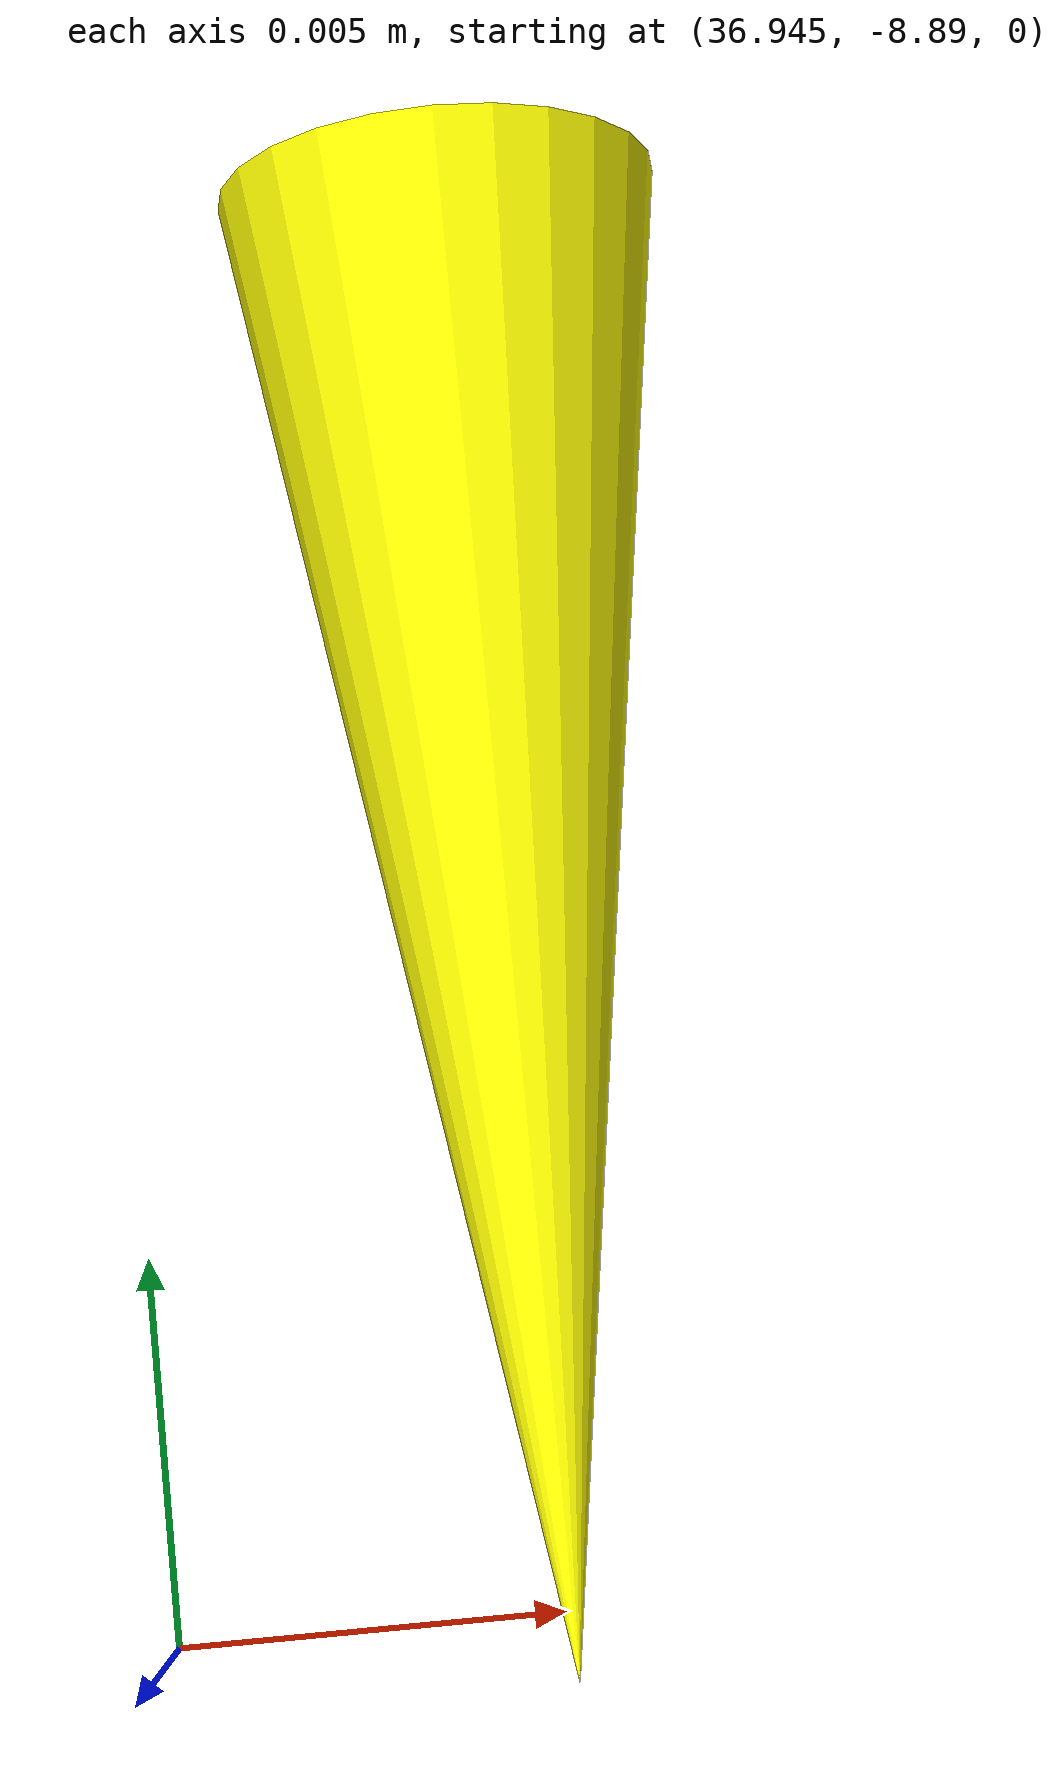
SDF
<?xml version="1.0"?>

<sdf version='1.9'>
     <model name='cone_0'>
      <link name='cone_0_link'>
        <inertial>
			<mass>0</mass>
			<inertia>
			<ixx>0.166667</ixx>
			<ixy>0</ixy>
			<ixz>0</ixz>
			<iyy>0.166667</iyy>
			<iyz>0</iyz>
			<izz>0.166667</izz>
			</inertia>
		</inertial>
        <collision name='cone_0_collision'>
          <geometry>
            <mesh>
              <uri>/models/cone/meshes/cone.stl</uri>
              <scale>0.001 0.001 0.001</scale>
            </mesh>
          </geometry>
        </collision>
        <visual name='cone_0_visual'>
          <geometry>
            <mesh>
              <uri>/models/cone/meshes/cone.stl</uri>
              <scale>0.001 0.001 0.001</scale>
            </mesh>
          </geometry>
          <material>
            <ambient>1 1 0 1</ambient>
            <diffuse>1 1 0 1</diffuse>
            <specular>1 1 0 1</specular>
          </material>
        </visual>

        <enable_wind>false</enable_wind>
      </link>
      <pose>38.0 0.0 0.0 1.57 0 0</pose>
      <static>true</static>
      </model>

     <model name='cone_1'>
      <link name='cone_1_link'>
        <inertial>
			<mass>0</mass>
			<inertia>
			<ixx>0.166667</ixx>
			<ixy>0</ixy>
			<ixz>0</ixz>
			<iyy>0.166667</iyy>
			<iyz>0</iyz>
			<izz>0.166667</izz>
			</inertia>
		</inertial>
        <collision name='cone_1_collision'>
          <geometry>
            <mesh>
              <uri>/models/cone/meshes/cone.stl</uri>
              <scale>0.001 0.001 0.001</scale>
            </mesh>
          </geometry>
        </collision>
        <visual name='cone_1_visual'>
          <geometry>
            <mesh>
              <uri>/models/cone/meshes/cone.stl</uri>
              <scale>0.001 0.001 0.001</scale>
            </mesh>
          </geometry>
          <material>
            <ambient>1 1 0 1</ambient>
            <diffuse>1 1 0 1</diffuse>
            <specular>1 1 0 1</specular>
          </material>
        </visual>

        <enable_wind>false</enable_wind>
      </link>
      <pose>37.88285868185886 2.981445637658108 0.0 1.57 0 0</pose>
      <static>true</static>
      </model>

     <model name='cone_2'>
      <link name='cone_2_link'>
        <inertial>
			<mass>0</mass>
			<inertia>
			<ixx>0.166667</ixx>
			<ixy>0</ixy>
			<ixz>0</ixz>
			<iyy>0.166667</iyy>
			<iyz>0</iyz>
			<izz>0.166667</izz>
			</inertia>
		</inertial>
        <collision name='cone_2_collision'>
          <geometry>
            <mesh>
              <uri>/models/cone/meshes/cone.stl</uri>
              <scale>0.001 0.001 0.001</scale>
            </mesh>
          </geometry>
        </collision>
        <visual name='cone_2_visual'>
          <geometry>
            <mesh>
              <uri>/models/cone/meshes/cone.stl</uri>
              <scale>0.001 0.001 0.001</scale>
            </mesh>
          </geometry>
          <material>
            <ambient>1 1 0 1</ambient>
            <diffuse>1 1 0 1</diffuse>
            <specular>1 1 0 1</specular>
          </material>
        </visual>

        <enable_wind>false</enable_wind>
      </link>
      <pose>37.53215694261524 5.944509671528773 0.0 1.57 0 0</pose>
      <static>true</static>
      </model>

     <model name='cone_3'>
      <link name='cone_3_link'>
        <inertial>
			<mass>0</mass>
			<inertia>
			<ixx>0.166667</ixx>
			<ixy>0</ixy>
			<ixz>0</ixz>
			<iyy>0.166667</iyy>
			<iyz>0</iyz>
			<izz>0.166667</izz>
			</inertia>
		</inertial>
        <collision name='cone_3_collision'>
          <geometry>
            <mesh>
              <uri>/models/cone/meshes/cone.stl</uri>
              <scale>0.001 0.001 0.001</scale>
            </mesh>
          </geometry>
        </collision>
        <visual name='cone_3_visual'>
          <geometry>
            <mesh>
              <uri>/models/cone/meshes/cone.stl</uri>
              <scale>0.001 0.001 0.001</scale>
            </mesh>
          </geometry>
          <material>
            <ambient>1 1 0 1</ambient>
            <diffuse>1 1 0 1</diffuse>
            <specular>1 1 0 1</specular>
          </material>
        </visual>

        <enable_wind>false</enable_wind>
      </link>
      <pose>36.95005697511171 8.870923826524406 0.0 1.57 0 0</pose>
      <static>true</static>
      </model>

     <model name='cone_4'>
      <link name='cone_4_link'>
        <inertial>
			<mass>0</mass>
			<inertia>
			<ixx>0.166667</ixx>
			<ixy>0</ixy>
			<ixz>0</ixz>
			<iyy>0.166667</iyy>
			<iyz>0</iyz>
			<izz>0.166667</izz>
			</inertia>
		</inertial>
        <collision name='cone_4_collision'>
          <geometry>
            <mesh>
              <uri>/models/cone/meshes/cone.stl</uri>
              <scale>0.001 0.001 0.001</scale>
            </mesh>
          </geometry>
        </collision>
        <visual name='cone_4_visual'>
          <geometry>
            <mesh>
              <uri>/models/cone/meshes/cone.stl</uri>
              <scale>0.001 0.001 0.001</scale>
            </mesh>
          </geometry>
          <material>
            <ambient>1 1 0 1</ambient>
            <diffuse>1 1 0 1</diffuse>
            <specular>1 1 0 1</specular>
          </material>
        </visual>

        <enable_wind>false</enable_wind>
      </link>
      <pose>36.14014761921583 11.742645786248001 0.0 1.57 0 0</pose>
      <static>true</static>
      </model>

     <model name='cone_5'>
      <link name='cone_5_link'>
        <inertial>
			<mass>0</mass>
			<inertia>
			<ixx>0.166667</ixx>
			<ixy>0</ixy>
			<ixz>0</ixz>
			<iyy>0.166667</iyy>
			<iyz>0</iyz>
			<izz>0.166667</izz>
			</inertia>
		</inertial>
        <collision name='cone_5_collision'>
          <geometry>
            <mesh>
              <uri>/models/cone/meshes/cone.stl</uri>
              <scale>0.001 0.001 0.001</scale>
            </mesh>
          </geometry>
        </collision>
        <visual name='cone_5_visual'>
          <geometry>
            <mesh>
              <uri>/models/cone/meshes/cone.stl</uri>
              <scale>0.001 0.001 0.001</scale>
            </mesh>
          </geometry>
          <material>
            <ambient>1 1 0 1</ambient>
            <diffuse>1 1 0 1</diffuse>
            <specular>1 1 0 1</specular>
          </material>
        </visual>

        <enable_wind>false</enable_wind>
      </link>
      <pose>35.1074222354289 14.541970429873412 0.0 1.57 0 0</pose>
      <static>true</static>
      </model>

     <model name='cone_6'>
      <link name='cone_6_link'>
        <inertial>
			<mass>0</mass>
			<inertia>
			<ixx>0.166667</ixx>
			<ixy>0</ixy>
			<ixz>0</ixz>
			<iyy>0.166667</iyy>
			<iyz>0</iyz>
			<izz>0.166667</izz>
			</inertia>
		</inertial>
        <collision name='cone_6_collision'>
          <geometry>
            <mesh>
              <uri>/models/cone/meshes/cone.stl</uri>
              <scale>0.001 0.001 0.001</scale>
            </mesh>
          </geometry>
        </collision>
        <visual name='cone_6_visual'>
          <geometry>
            <mesh>
              <uri>/models/cone/meshes/cone.stl</uri>
              <scale>0.001 0.001 0.001</scale>
            </mesh>
          </geometry>
          <material>
            <ambient>1 1 0 1</ambient>
            <diffuse>1 1 0 1</diffuse>
            <specular>1 1 0 1</specular>
          </material>
        </visual>

        <enable_wind>false</enable_wind>
      </link>
      <pose>33.85824791915798 17.251638990102776 0.0 1.57 0 0</pose>
      <static>true</static>
      </model>

     <model name='cone_7'>
      <link name='cone_7_link'>
        <inertial>
			<mass>0</mass>
			<inertia>
			<ixx>0.166667</ixx>
			<ixy>0</ixy>
			<ixz>0</ixz>
			<iyy>0.166667</iyy>
			<iyz>0</iyz>
			<izz>0.166667</izz>
			</inertia>
		</inertial>
        <collision name='cone_7_collision'>
          <geometry>
            <mesh>
              <uri>/models/cone/meshes/cone.stl</uri>
              <scale>0.001 0.001 0.001</scale>
            </mesh>
          </geometry>
        </collision>
        <visual name='cone_7_visual'>
          <geometry>
            <mesh>
              <uri>/models/cone/meshes/cone.stl</uri>
              <scale>0.001 0.001 0.001</scale>
            </mesh>
          </geometry>
          <material>
            <ambient>1 1 0 1</ambient>
            <diffuse>1 1 0 1</diffuse>
            <specular>1 1 0 1</specular>
          </material>
        </visual>

        <enable_wind>false</enable_wind>
      </link>
      <pose>32.4003262454555 19.854945459206053 0.0 1.57 0 0</pose>
      <static>true</static>
      </model>

     <model name='cone_8'>
      <link name='cone_8_link'>
        <inertial>
			<mass>0</mass>
			<inertia>
			<ixx>0.166667</ixx>
			<ixy>0</ixy>
			<ixz>0</ixz>
			<iyy>0.166667</iyy>
			<iyz>0</iyz>
			<izz>0.166667</izz>
			</inertia>
		</inertial>
        <collision name='cone_8_collision'>
          <geometry>
            <mesh>
              <uri>/models/cone/meshes/cone.stl</uri>
              <scale>0.001 0.001 0.001</scale>
            </mesh>
          </geometry>
        </collision>
        <visual name='cone_8_visual'>
          <geometry>
            <mesh>
              <uri>/models/cone/meshes/cone.stl</uri>
              <scale>0.001 0.001 0.001</scale>
            </mesh>
          </geometry>
          <material>
            <ambient>1 1 0 1</ambient>
            <diffuse>1 1 0 1</diffuse>
            <specular>1 1 0 1</specular>
          </material>
        </visual>

        <enable_wind>false</enable_wind>
      </link>
      <pose>30.742645786248005 22.33583958711398 0.0 1.57 0 0</pose>
      <static>true</static>
      </model>

     <model name='cone_9'>
      <link name='cone_9_link'>
        <inertial>
			<mass>0</mass>
			<inertia>
			<ixx>0.166667</ixx>
			<ixy>0</ixy>
			<ixz>0</ixz>
			<iyy>0.166667</iyy>
			<iyz>0</iyz>
			<izz>0.166667</izz>
			</inertia>
		</inertial>
        <collision name='cone_9_collision'>
          <geometry>
            <mesh>
              <uri>/models/cone/meshes/cone.stl</uri>
              <scale>0.001 0.001 0.001</scale>
            </mesh>
          </geometry>
        </collision>
        <visual name='cone_9_visual'>
          <geometry>
            <mesh>
              <uri>/models/cone/meshes/cone.stl</uri>
              <scale>0.001 0.001 0.001</scale>
            </mesh>
          </geometry>
          <material>
            <ambient>1 1 0 1</ambient>
            <diffuse>1 1 0 1</diffuse>
            <specular>1 1 0 1</specular>
          </material>
        </visual>

        <enable_wind>false</enable_wind>
      </link>
      <pose>28.895426692801177 24.67902583654698 0.0 1.57 0 0</pose>
      <static>true</static>
      </model>

     <model name='cone_10'>
      <link name='cone_10_link'>
        <inertial>
			<mass>0</mass>
			<inertia>
			<ixx>0.166667</ixx>
			<ixy>0</ixy>
			<ixz>0</ixz>
			<iyy>0.166667</iyy>
			<iyz>0</iyz>
			<izz>0.166667</izz>
			</inertia>
		</inertial>
        <collision name='cone_10_collision'>
          <geometry>
            <mesh>
              <uri>/models/cone/meshes/cone.stl</uri>
              <scale>0.001 0.001 0.001</scale>
            </mesh>
          </geometry>
        </collision>
        <visual name='cone_10_visual'>
          <geometry>
            <mesh>
              <uri>/models/cone/meshes/cone.stl</uri>
              <scale>0.001 0.001 0.001</scale>
            </mesh>
          </geometry>
          <material>
            <ambient>1 1 0 1</ambient>
            <diffuse>1 1 0 1</diffuse>
            <specular>1 1 0 1</specular>
          </material>
        </visual>

        <enable_wind>false</enable_wind>
      </link>
      <pose>26.870057685088806 26.870057685088803 0.0 1.57 0 0</pose>
      <static>true</static>
      </model>

     <model name='cone_11'>
      <link name='cone_11_link'>
        <inertial>
			<mass>0</mass>
			<inertia>
			<ixx>0.166667</ixx>
			<ixy>0</ixy>
			<ixz>0</ixz>
			<iyy>0.166667</iyy>
			<iyz>0</iyz>
			<izz>0.166667</izz>
			</inertia>
		</inertial>
        <collision name='cone_11_collision'>
          <geometry>
            <mesh>
              <uri>/models/cone/meshes/cone.stl</uri>
              <scale>0.001 0.001 0.001</scale>
            </mesh>
          </geometry>
        </collision>
        <visual name='cone_11_visual'>
          <geometry>
            <mesh>
              <uri>/models/cone/meshes/cone.stl</uri>
              <scale>0.001 0.001 0.001</scale>
            </mesh>
          </geometry>
          <material>
            <ambient>1 1 0 1</ambient>
            <diffuse>1 1 0 1</diffuse>
            <specular>1 1 0 1</specular>
          </material>
        </visual>

        <enable_wind>false</enable_wind>
      </link>
      <pose>24.67902583654698 28.895426692801177 0.0 1.57 0 0</pose>
      <static>true</static>
      </model>

     <model name='cone_12'>
      <link name='cone_12_link'>
        <inertial>
			<mass>0</mass>
			<inertia>
			<ixx>0.166667</ixx>
			<ixy>0</ixy>
			<ixz>0</ixz>
			<iyy>0.166667</iyy>
			<iyz>0</iyz>
			<izz>0.166667</izz>
			</inertia>
		</inertial>
        <collision name='cone_12_collision'>
          <geometry>
            <mesh>
              <uri>/models/cone/meshes/cone.stl</uri>
              <scale>0.001 0.001 0.001</scale>
            </mesh>
          </geometry>
        </collision>
        <visual name='cone_12_visual'>
          <geometry>
            <mesh>
              <uri>/models/cone/meshes/cone.stl</uri>
              <scale>0.001 0.001 0.001</scale>
            </mesh>
          </geometry>
          <material>
            <ambient>1 1 0 1</ambient>
            <diffuse>1 1 0 1</diffuse>
            <specular>1 1 0 1</specular>
          </material>
        </visual>

        <enable_wind>false</enable_wind>
      </link>
      <pose>22.33583958711398 30.742645786248005 0.0 1.57 0 0</pose>
      <static>true</static>
      </model>

     <model name='cone_13'>
      <link name='cone_13_link'>
        <inertial>
			<mass>0</mass>
			<inertia>
			<ixx>0.166667</ixx>
			<ixy>0</ixy>
			<ixz>0</ixz>
			<iyy>0.166667</iyy>
			<iyz>0</iyz>
			<izz>0.166667</izz>
			</inertia>
		</inertial>
        <collision name='cone_13_collision'>
          <geometry>
            <mesh>
              <uri>/models/cone/meshes/cone.stl</uri>
              <scale>0.001 0.001 0.001</scale>
            </mesh>
          </geometry>
        </collision>
        <visual name='cone_13_visual'>
          <geometry>
            <mesh>
              <uri>/models/cone/meshes/cone.stl</uri>
              <scale>0.001 0.001 0.001</scale>
            </mesh>
          </geometry>
          <material>
            <ambient>1 1 0 1</ambient>
            <diffuse>1 1 0 1</diffuse>
            <specular>1 1 0 1</specular>
          </material>
        </visual>

        <enable_wind>false</enable_wind>
      </link>
      <pose>19.854945459206057 32.4003262454555 0.0 1.57 0 0</pose>
      <static>true</static>
      </model>

     <model name='cone_14'>
      <link name='cone_14_link'>
        <inertial>
			<mass>0</mass>
			<inertia>
			<ixx>0.166667</ixx>
			<ixy>0</ixy>
			<ixz>0</ixz>
			<iyy>0.166667</iyy>
			<iyz>0</iyz>
			<izz>0.166667</izz>
			</inertia>
		</inertial>
        <collision name='cone_14_collision'>
          <geometry>
            <mesh>
              <uri>/models/cone/meshes/cone.stl</uri>
              <scale>0.001 0.001 0.001</scale>
            </mesh>
          </geometry>
        </collision>
        <visual name='cone_14_visual'>
          <geometry>
            <mesh>
              <uri>/models/cone/meshes/cone.stl</uri>
              <scale>0.001 0.001 0.001</scale>
            </mesh>
          </geometry>
          <material>
            <ambient>1 1 0 1</ambient>
            <diffuse>1 1 0 1</diffuse>
            <specular>1 1 0 1</specular>
          </material>
        </visual>

        <enable_wind>false</enable_wind>
      </link>
      <pose>17.25163899010278 33.858247919157975 0.0 1.57 0 0</pose>
      <static>true</static>
      </model>

     <model name='cone_15'>
      <link name='cone_15_link'>
        <inertial>
			<mass>0</mass>
			<inertia>
			<ixx>0.166667</ixx>
			<ixy>0</ixy>
			<ixz>0</ixz>
			<iyy>0.166667</iyy>
			<iyz>0</iyz>
			<izz>0.166667</izz>
			</inertia>
		</inertial>
        <collision name='cone_15_collision'>
          <geometry>
            <mesh>
              <uri>/models/cone/meshes/cone.stl</uri>
              <scale>0.001 0.001 0.001</scale>
            </mesh>
          </geometry>
        </collision>
        <visual name='cone_15_visual'>
          <geometry>
            <mesh>
              <uri>/models/cone/meshes/cone.stl</uri>
              <scale>0.001 0.001 0.001</scale>
            </mesh>
          </geometry>
          <material>
            <ambient>1 1 0 1</ambient>
            <diffuse>1 1 0 1</diffuse>
            <specular>1 1 0 1</specular>
          </material>
        </visual>

        <enable_wind>false</enable_wind>
      </link>
      <pose>14.541970429873414 35.1074222354289 0.0 1.57 0 0</pose>
      <static>true</static>
      </model>

     <model name='cone_16'>
      <link name='cone_16_link'>
        <inertial>
			<mass>0</mass>
			<inertia>
			<ixx>0.166667</ixx>
			<ixy>0</ixy>
			<ixz>0</ixz>
			<iyy>0.166667</iyy>
			<iyz>0</iyz>
			<izz>0.166667</izz>
			</inertia>
		</inertial>
        <collision name='cone_16_collision'>
          <geometry>
            <mesh>
              <uri>/models/cone/meshes/cone.stl</uri>
              <scale>0.001 0.001 0.001</scale>
            </mesh>
          </geometry>
        </collision>
        <visual name='cone_16_visual'>
          <geometry>
            <mesh>
              <uri>/models/cone/meshes/cone.stl</uri>
              <scale>0.001 0.001 0.001</scale>
            </mesh>
          </geometry>
          <material>
            <ambient>1 1 0 1</ambient>
            <diffuse>1 1 0 1</diffuse>
            <specular>1 1 0 1</specular>
          </material>
        </visual>

        <enable_wind>false</enable_wind>
      </link>
      <pose>11.742645786248003 36.14014761921583 0.0 1.57 0 0</pose>
      <static>true</static>
      </model>

     <model name='cone_17'>
      <link name='cone_17_link'>
        <inertial>
			<mass>0</mass>
			<inertia>
			<ixx>0.166667</ixx>
			<ixy>0</ixy>
			<ixz>0</ixz>
			<iyy>0.166667</iyy>
			<iyz>0</iyz>
			<izz>0.166667</izz>
			</inertia>
		</inertial>
        <collision name='cone_17_collision'>
          <geometry>
            <mesh>
              <uri>/models/cone/meshes/cone.stl</uri>
              <scale>0.001 0.001 0.001</scale>
            </mesh>
          </geometry>
        </collision>
        <visual name='cone_17_visual'>
          <geometry>
            <mesh>
              <uri>/models/cone/meshes/cone.stl</uri>
              <scale>0.001 0.001 0.001</scale>
            </mesh>
          </geometry>
          <material>
            <ambient>1 1 0 1</ambient>
            <diffuse>1 1 0 1</diffuse>
            <specular>1 1 0 1</specular>
          </material>
        </visual>

        <enable_wind>false</enable_wind>
      </link>
      <pose>8.870923826524407 36.95005697511171 0.0 1.57 0 0</pose>
      <static>true</static>
      </model>

     <model name='cone_18'>
      <link name='cone_18_link'>
        <inertial>
			<mass>0</mass>
			<inertia>
			<ixx>0.166667</ixx>
			<ixy>0</ixy>
			<ixz>0</ixz>
			<iyy>0.166667</iyy>
			<iyz>0</iyz>
			<izz>0.166667</izz>
			</inertia>
		</inertial>
        <collision name='cone_18_collision'>
          <geometry>
            <mesh>
              <uri>/models/cone/meshes/cone.stl</uri>
              <scale>0.001 0.001 0.001</scale>
            </mesh>
          </geometry>
        </collision>
        <visual name='cone_18_visual'>
          <geometry>
            <mesh>
              <uri>/models/cone/meshes/cone.stl</uri>
              <scale>0.001 0.001 0.001</scale>
            </mesh>
          </geometry>
          <material>
            <ambient>1 1 0 1</ambient>
            <diffuse>1 1 0 1</diffuse>
            <specular>1 1 0 1</specular>
          </material>
        </visual>

        <enable_wind>false</enable_wind>
      </link>
      <pose>5.944509671528775 37.53215694261524 0.0 1.57 0 0</pose>
      <static>true</static>
      </model>

     <model name='cone_19'>
      <link name='cone_19_link'>
        <inertial>
			<mass>0</mass>
			<inertia>
			<ixx>0.166667</ixx>
			<ixy>0</ixy>
			<ixz>0</ixz>
			<iyy>0.166667</iyy>
			<iyz>0</iyz>
			<izz>0.166667</izz>
			</inertia>
		</inertial>
        <collision name='cone_19_collision'>
          <geometry>
            <mesh>
              <uri>/models/cone/meshes/cone.stl</uri>
              <scale>0.001 0.001 0.001</scale>
            </mesh>
          </geometry>
        </collision>
        <visual name='cone_19_visual'>
          <geometry>
            <mesh>
              <uri>/models/cone/meshes/cone.stl</uri>
              <scale>0.001 0.001 0.001</scale>
            </mesh>
          </geometry>
          <material>
            <ambient>1 1 0 1</ambient>
            <diffuse>1 1 0 1</diffuse>
            <specular>1 1 0 1</specular>
          </material>
        </visual>

        <enable_wind>false</enable_wind>
      </link>
      <pose>2.9814456376581098 37.88285868185886 0.0 1.57 0 0</pose>
      <static>true</static>
      </model>

     <model name='cone_20'>
      <link name='cone_20_link'>
        <inertial>
			<mass>0</mass>
			<inertia>
			<ixx>0.166667</ixx>
			<ixy>0</ixy>
			<ixz>0</ixz>
			<iyy>0.166667</iyy>
			<iyz>0</iyz>
			<izz>0.166667</izz>
			</inertia>
		</inertial>
        <collision name='cone_20_collision'>
          <geometry>
            <mesh>
              <uri>/models/cone/meshes/cone.stl</uri>
              <scale>0.001 0.001 0.001</scale>
            </mesh>
          </geometry>
        </collision>
        <visual name='cone_20_visual'>
          <geometry>
            <mesh>
              <uri>/models/cone/meshes/cone.stl</uri>
              <scale>0.001 0.001 0.001</scale>
            </mesh>
          </geometry>
          <material>
            <ambient>1 1 0 1</ambient>
            <diffuse>1 1 0 1</diffuse>
            <specular>1 1 0 1</specular>
          </material>
        </visual>

        <enable_wind>false</enable_wind>
      </link>
      <pose>2.326828918379971e-15 38.0 0.0 1.57 0 0</pose>
      <static>true</static>
      </model>

     <model name='cone_21'>
      <link name='cone_21_link'>
        <inertial>
			<mass>0</mass>
			<inertia>
			<ixx>0.166667</ixx>
			<ixy>0</ixy>
			<ixz>0</ixz>
			<iyy>0.166667</iyy>
			<iyz>0</iyz>
			<izz>0.166667</izz>
			</inertia>
		</inertial>
        <collision name='cone_21_collision'>
          <geometry>
            <mesh>
              <uri>/models/cone/meshes/cone.stl</uri>
              <scale>0.001 0.001 0.001</scale>
            </mesh>
          </geometry>
        </collision>
        <visual name='cone_21_visual'>
          <geometry>
            <mesh>
              <uri>/models/cone/meshes/cone.stl</uri>
              <scale>0.001 0.001 0.001</scale>
            </mesh>
          </geometry>
          <material>
            <ambient>1 1 0 1</ambient>
            <diffuse>1 1 0 1</diffuse>
            <specular>1 1 0 1</specular>
          </material>
        </visual>

        <enable_wind>false</enable_wind>
      </link>
      <pose>-2.9814456376581053 37.88285868185886 0.0 1.57 0 0</pose>
      <static>true</static>
      </model>

     <model name='cone_22'>
      <link name='cone_22_link'>
        <inertial>
			<mass>0</mass>
			<inertia>
			<ixx>0.166667</ixx>
			<ixy>0</ixy>
			<ixz>0</ixz>
			<iyy>0.166667</iyy>
			<iyz>0</iyz>
			<izz>0.166667</izz>
			</inertia>
		</inertial>
        <collision name='cone_22_collision'>
          <geometry>
            <mesh>
              <uri>/models/cone/meshes/cone.stl</uri>
              <scale>0.001 0.001 0.001</scale>
            </mesh>
          </geometry>
        </collision>
        <visual name='cone_22_visual'>
          <geometry>
            <mesh>
              <uri>/models/cone/meshes/cone.stl</uri>
              <scale>0.001 0.001 0.001</scale>
            </mesh>
          </geometry>
          <material>
            <ambient>1 1 0 1</ambient>
            <diffuse>1 1 0 1</diffuse>
            <specular>1 1 0 1</specular>
          </material>
        </visual>

        <enable_wind>false</enable_wind>
      </link>
      <pose>-5.944509671528771 37.53215694261524 0.0 1.57 0 0</pose>
      <static>true</static>
      </model>

     <model name='cone_23'>
      <link name='cone_23_link'>
        <inertial>
			<mass>0</mass>
			<inertia>
			<ixx>0.166667</ixx>
			<ixy>0</ixy>
			<ixz>0</ixz>
			<iyy>0.166667</iyy>
			<iyz>0</iyz>
			<izz>0.166667</izz>
			</inertia>
		</inertial>
        <collision name='cone_23_collision'>
          <geometry>
            <mesh>
              <uri>/models/cone/meshes/cone.stl</uri>
              <scale>0.001 0.001 0.001</scale>
            </mesh>
          </geometry>
        </collision>
        <visual name='cone_23_visual'>
          <geometry>
            <mesh>
              <uri>/models/cone/meshes/cone.stl</uri>
              <scale>0.001 0.001 0.001</scale>
            </mesh>
          </geometry>
          <material>
            <ambient>1 1 0 1</ambient>
            <diffuse>1 1 0 1</diffuse>
            <specular>1 1 0 1</specular>
          </material>
        </visual>

        <enable_wind>false</enable_wind>
      </link>
      <pose>-8.870923826524402 36.950056975111714 0.0 1.57 0 0</pose>
      <static>true</static>
      </model>

     <model name='cone_24'>
      <link name='cone_24_link'>
        <inertial>
			<mass>0</mass>
			<inertia>
			<ixx>0.166667</ixx>
			<ixy>0</ixy>
			<ixz>0</ixz>
			<iyy>0.166667</iyy>
			<iyz>0</iyz>
			<izz>0.166667</izz>
			</inertia>
		</inertial>
        <collision name='cone_24_collision'>
          <geometry>
            <mesh>
              <uri>/models/cone/meshes/cone.stl</uri>
              <scale>0.001 0.001 0.001</scale>
            </mesh>
          </geometry>
        </collision>
        <visual name='cone_24_visual'>
          <geometry>
            <mesh>
              <uri>/models/cone/meshes/cone.stl</uri>
              <scale>0.001 0.001 0.001</scale>
            </mesh>
          </geometry>
          <material>
            <ambient>1 1 0 1</ambient>
            <diffuse>1 1 0 1</diffuse>
            <specular>1 1 0 1</specular>
          </material>
        </visual>

        <enable_wind>false</enable_wind>
      </link>
      <pose>-11.742645786248 36.14014761921584 0.0 1.57 0 0</pose>
      <static>true</static>
      </model>

     <model name='cone_25'>
      <link name='cone_25_link'>
        <inertial>
			<mass>0</mass>
			<inertia>
			<ixx>0.166667</ixx>
			<ixy>0</ixy>
			<ixz>0</ixz>
			<iyy>0.166667</iyy>
			<iyz>0</iyz>
			<izz>0.166667</izz>
			</inertia>
		</inertial>
        <collision name='cone_25_collision'>
          <geometry>
            <mesh>
              <uri>/models/cone/meshes/cone.stl</uri>
              <scale>0.001 0.001 0.001</scale>
            </mesh>
          </geometry>
        </collision>
        <visual name='cone_25_visual'>
          <geometry>
            <mesh>
              <uri>/models/cone/meshes/cone.stl</uri>
              <scale>0.001 0.001 0.001</scale>
            </mesh>
          </geometry>
          <material>
            <ambient>1 1 0 1</ambient>
            <diffuse>1 1 0 1</diffuse>
            <specular>1 1 0 1</specular>
          </material>
        </visual>

        <enable_wind>false</enable_wind>
      </link>
      <pose>-14.541970429873409 35.1074222354289 0.0 1.57 0 0</pose>
      <static>true</static>
      </model>

     <model name='cone_26'>
      <link name='cone_26_link'>
        <inertial>
			<mass>0</mass>
			<inertia>
			<ixx>0.166667</ixx>
			<ixy>0</ixy>
			<ixz>0</ixz>
			<iyy>0.166667</iyy>
			<iyz>0</iyz>
			<izz>0.166667</izz>
			</inertia>
		</inertial>
        <collision name='cone_26_collision'>
          <geometry>
            <mesh>
              <uri>/models/cone/meshes/cone.stl</uri>
              <scale>0.001 0.001 0.001</scale>
            </mesh>
          </geometry>
        </collision>
        <visual name='cone_26_visual'>
          <geometry>
            <mesh>
              <uri>/models/cone/meshes/cone.stl</uri>
              <scale>0.001 0.001 0.001</scale>
            </mesh>
          </geometry>
          <material>
            <ambient>1 1 0 1</ambient>
            <diffuse>1 1 0 1</diffuse>
            <specular>1 1 0 1</specular>
          </material>
        </visual>

        <enable_wind>false</enable_wind>
      </link>
      <pose>-17.251638990102773 33.85824791915798 0.0 1.57 0 0</pose>
      <static>true</static>
      </model>

     <model name='cone_27'>
      <link name='cone_27_link'>
        <inertial>
			<mass>0</mass>
			<inertia>
			<ixx>0.166667</ixx>
			<ixy>0</ixy>
			<ixz>0</ixz>
			<iyy>0.166667</iyy>
			<iyz>0</iyz>
			<izz>0.166667</izz>
			</inertia>
		</inertial>
        <collision name='cone_27_collision'>
          <geometry>
            <mesh>
              <uri>/models/cone/meshes/cone.stl</uri>
              <scale>0.001 0.001 0.001</scale>
            </mesh>
          </geometry>
        </collision>
        <visual name='cone_27_visual'>
          <geometry>
            <mesh>
              <uri>/models/cone/meshes/cone.stl</uri>
              <scale>0.001 0.001 0.001</scale>
            </mesh>
          </geometry>
          <material>
            <ambient>1 1 0 1</ambient>
            <diffuse>1 1 0 1</diffuse>
            <specular>1 1 0 1</specular>
          </material>
        </visual>

        <enable_wind>false</enable_wind>
      </link>
      <pose>-19.854945459206053 32.40032624545551 0.0 1.57 0 0</pose>
      <static>true</static>
      </model>

     <model name='cone_28'>
      <link name='cone_28_link'>
        <inertial>
			<mass>0</mass>
			<inertia>
			<ixx>0.166667</ixx>
			<ixy>0</ixy>
			<ixz>0</ixz>
			<iyy>0.166667</iyy>
			<iyz>0</iyz>
			<izz>0.166667</izz>
			</inertia>
		</inertial>
        <collision name='cone_28_collision'>
          <geometry>
            <mesh>
              <uri>/models/cone/meshes/cone.stl</uri>
              <scale>0.001 0.001 0.001</scale>
            </mesh>
          </geometry>
        </collision>
        <visual name='cone_28_visual'>
          <geometry>
            <mesh>
              <uri>/models/cone/meshes/cone.stl</uri>
              <scale>0.001 0.001 0.001</scale>
            </mesh>
          </geometry>
          <material>
            <ambient>1 1 0 1</ambient>
            <diffuse>1 1 0 1</diffuse>
            <specular>1 1 0 1</specular>
          </material>
        </visual>

        <enable_wind>false</enable_wind>
      </link>
      <pose>-22.335839587113973 30.742645786248005 0.0 1.57 0 0</pose>
      <static>true</static>
      </model>

     <model name='cone_29'>
      <link name='cone_29_link'>
        <inertial>
			<mass>0</mass>
			<inertia>
			<ixx>0.166667</ixx>
			<ixy>0</ixy>
			<ixz>0</ixz>
			<iyy>0.166667</iyy>
			<iyz>0</iyz>
			<izz>0.166667</izz>
			</inertia>
		</inertial>
        <collision name='cone_29_collision'>
          <geometry>
            <mesh>
              <uri>/models/cone/meshes/cone.stl</uri>
              <scale>0.001 0.001 0.001</scale>
            </mesh>
          </geometry>
        </collision>
        <visual name='cone_29_visual'>
          <geometry>
            <mesh>
              <uri>/models/cone/meshes/cone.stl</uri>
              <scale>0.001 0.001 0.001</scale>
            </mesh>
          </geometry>
          <material>
            <ambient>1 1 0 1</ambient>
            <diffuse>1 1 0 1</diffuse>
            <specular>1 1 0 1</specular>
          </material>
        </visual>

        <enable_wind>false</enable_wind>
      </link>
      <pose>-24.679025836546973 28.89542669280118 0.0 1.57 0 0</pose>
      <static>true</static>
      </model>

     <model name='cone_30'>
      <link name='cone_30_link'>
        <inertial>
			<mass>0</mass>
			<inertia>
			<ixx>0.166667</ixx>
			<ixy>0</ixy>
			<ixz>0</ixz>
			<iyy>0.166667</iyy>
			<iyz>0</iyz>
			<izz>0.166667</izz>
			</inertia>
		</inertial>
        <collision name='cone_30_collision'>
          <geometry>
            <mesh>
              <uri>/models/cone/meshes/cone.stl</uri>
              <scale>0.001 0.001 0.001</scale>
            </mesh>
          </geometry>
        </collision>
        <visual name='cone_30_visual'>
          <geometry>
            <mesh>
              <uri>/models/cone/meshes/cone.stl</uri>
              <scale>0.001 0.001 0.001</scale>
            </mesh>
          </geometry>
          <material>
            <ambient>1 1 0 1</ambient>
            <diffuse>1 1 0 1</diffuse>
            <specular>1 1 0 1</specular>
          </material>
        </visual>

        <enable_wind>false</enable_wind>
      </link>
      <pose>-26.870057685088803 26.870057685088806 0.0 1.57 0 0</pose>
      <static>true</static>
      </model>

     <model name='cone_31'>
      <link name='cone_31_link'>
        <inertial>
			<mass>0</mass>
			<inertia>
			<ixx>0.166667</ixx>
			<ixy>0</ixy>
			<ixz>0</ixz>
			<iyy>0.166667</iyy>
			<iyz>0</iyz>
			<izz>0.166667</izz>
			</inertia>
		</inertial>
        <collision name='cone_31_collision'>
          <geometry>
            <mesh>
              <uri>/models/cone/meshes/cone.stl</uri>
              <scale>0.001 0.001 0.001</scale>
            </mesh>
          </geometry>
        </collision>
        <visual name='cone_31_visual'>
          <geometry>
            <mesh>
              <uri>/models/cone/meshes/cone.stl</uri>
              <scale>0.001 0.001 0.001</scale>
            </mesh>
          </geometry>
          <material>
            <ambient>1 1 0 1</ambient>
            <diffuse>1 1 0 1</diffuse>
            <specular>1 1 0 1</specular>
          </material>
        </visual>

        <enable_wind>false</enable_wind>
      </link>
      <pose>-28.895426692801177 24.679025836546984 0.0 1.57 0 0</pose>
      <static>true</static>
      </model>

     <model name='cone_32'>
      <link name='cone_32_link'>
        <inertial>
			<mass>0</mass>
			<inertia>
			<ixx>0.166667</ixx>
			<ixy>0</ixy>
			<ixz>0</ixz>
			<iyy>0.166667</iyy>
			<iyz>0</iyz>
			<izz>0.166667</izz>
			</inertia>
		</inertial>
        <collision name='cone_32_collision'>
          <geometry>
            <mesh>
              <uri>/models/cone/meshes/cone.stl</uri>
              <scale>0.001 0.001 0.001</scale>
            </mesh>
          </geometry>
        </collision>
        <visual name='cone_32_visual'>
          <geometry>
            <mesh>
              <uri>/models/cone/meshes/cone.stl</uri>
              <scale>0.001 0.001 0.001</scale>
            </mesh>
          </geometry>
          <material>
            <ambient>1 1 0 1</ambient>
            <diffuse>1 1 0 1</diffuse>
            <specular>1 1 0 1</specular>
          </material>
        </visual>

        <enable_wind>false</enable_wind>
      </link>
      <pose>-30.742645786247998 22.335839587113984 0.0 1.57 0 0</pose>
      <static>true</static>
      </model>

     <model name='cone_33'>
      <link name='cone_33_link'>
        <inertial>
			<mass>0</mass>
			<inertia>
			<ixx>0.166667</ixx>
			<ixy>0</ixy>
			<ixz>0</ixz>
			<iyy>0.166667</iyy>
			<iyz>0</iyz>
			<izz>0.166667</izz>
			</inertia>
		</inertial>
        <collision name='cone_33_collision'>
          <geometry>
            <mesh>
              <uri>/models/cone/meshes/cone.stl</uri>
              <scale>0.001 0.001 0.001</scale>
            </mesh>
          </geometry>
        </collision>
        <visual name='cone_33_visual'>
          <geometry>
            <mesh>
              <uri>/models/cone/meshes/cone.stl</uri>
              <scale>0.001 0.001 0.001</scale>
            </mesh>
          </geometry>
          <material>
            <ambient>1 1 0 1</ambient>
            <diffuse>1 1 0 1</diffuse>
            <specular>1 1 0 1</specular>
          </material>
        </visual>

        <enable_wind>false</enable_wind>
      </link>
      <pose>-32.4003262454555 19.854945459206057 0.0 1.57 0 0</pose>
      <static>true</static>
      </model>

     <model name='cone_34'>
      <link name='cone_34_link'>
        <inertial>
			<mass>0</mass>
			<inertia>
			<ixx>0.166667</ixx>
			<ixy>0</ixy>
			<ixz>0</ixz>
			<iyy>0.166667</iyy>
			<iyz>0</iyz>
			<izz>0.166667</izz>
			</inertia>
		</inertial>
        <collision name='cone_34_collision'>
          <geometry>
            <mesh>
              <uri>/models/cone/meshes/cone.stl</uri>
              <scale>0.001 0.001 0.001</scale>
            </mesh>
          </geometry>
        </collision>
        <visual name='cone_34_visual'>
          <geometry>
            <mesh>
              <uri>/models/cone/meshes/cone.stl</uri>
              <scale>0.001 0.001 0.001</scale>
            </mesh>
          </geometry>
          <material>
            <ambient>1 1 0 1</ambient>
            <diffuse>1 1 0 1</diffuse>
            <specular>1 1 0 1</specular>
          </material>
        </visual>

        <enable_wind>false</enable_wind>
      </link>
      <pose>-33.858247919157975 17.25163899010278 0.0 1.57 0 0</pose>
      <static>true</static>
      </model>

     <model name='cone_35'>
      <link name='cone_35_link'>
        <inertial>
			<mass>0</mass>
			<inertia>
			<ixx>0.166667</ixx>
			<ixy>0</ixy>
			<ixz>0</ixz>
			<iyy>0.166667</iyy>
			<iyz>0</iyz>
			<izz>0.166667</izz>
			</inertia>
		</inertial>
        <collision name='cone_35_collision'>
          <geometry>
            <mesh>
              <uri>/models/cone/meshes/cone.stl</uri>
              <scale>0.001 0.001 0.001</scale>
            </mesh>
          </geometry>
        </collision>
        <visual name='cone_35_visual'>
          <geometry>
            <mesh>
              <uri>/models/cone/meshes/cone.stl</uri>
              <scale>0.001 0.001 0.001</scale>
            </mesh>
          </geometry>
          <material>
            <ambient>1 1 0 1</ambient>
            <diffuse>1 1 0 1</diffuse>
            <specular>1 1 0 1</specular>
          </material>
        </visual>

        <enable_wind>false</enable_wind>
      </link>
      <pose>-35.1074222354289 14.541970429873416 0.0 1.57 0 0</pose>
      <static>true</static>
      </model>

     <model name='cone_36'>
      <link name='cone_36_link'>
        <inertial>
			<mass>0</mass>
			<inertia>
			<ixx>0.166667</ixx>
			<ixy>0</ixy>
			<ixz>0</ixz>
			<iyy>0.166667</iyy>
			<iyz>0</iyz>
			<izz>0.166667</izz>
			</inertia>
		</inertial>
        <collision name='cone_36_collision'>
          <geometry>
            <mesh>
              <uri>/models/cone/meshes/cone.stl</uri>
              <scale>0.001 0.001 0.001</scale>
            </mesh>
          </geometry>
        </collision>
        <visual name='cone_36_visual'>
          <geometry>
            <mesh>
              <uri>/models/cone/meshes/cone.stl</uri>
              <scale>0.001 0.001 0.001</scale>
            </mesh>
          </geometry>
          <material>
            <ambient>1 1 0 1</ambient>
            <diffuse>1 1 0 1</diffuse>
            <specular>1 1 0 1</specular>
          </material>
        </visual>

        <enable_wind>false</enable_wind>
      </link>
      <pose>-36.14014761921583 11.742645786248005 0.0 1.57 0 0</pose>
      <static>true</static>
      </model>

     <model name='cone_37'>
      <link name='cone_37_link'>
        <inertial>
			<mass>0</mass>
			<inertia>
			<ixx>0.166667</ixx>
			<ixy>0</ixy>
			<ixz>0</ixz>
			<iyy>0.166667</iyy>
			<iyz>0</iyz>
			<izz>0.166667</izz>
			</inertia>
		</inertial>
        <collision name='cone_37_collision'>
          <geometry>
            <mesh>
              <uri>/models/cone/meshes/cone.stl</uri>
              <scale>0.001 0.001 0.001</scale>
            </mesh>
          </geometry>
        </collision>
        <visual name='cone_37_visual'>
          <geometry>
            <mesh>
              <uri>/models/cone/meshes/cone.stl</uri>
              <scale>0.001 0.001 0.001</scale>
            </mesh>
          </geometry>
          <material>
            <ambient>1 1 0 1</ambient>
            <diffuse>1 1 0 1</diffuse>
            <specular>1 1 0 1</specular>
          </material>
        </visual>

        <enable_wind>false</enable_wind>
      </link>
      <pose>-36.95005697511171 8.870923826524411 0.0 1.57 0 0</pose>
      <static>true</static>
      </model>

     <model name='cone_38'>
      <link name='cone_38_link'>
        <inertial>
			<mass>0</mass>
			<inertia>
			<ixx>0.166667</ixx>
			<ixy>0</ixy>
			<ixz>0</ixz>
			<iyy>0.166667</iyy>
			<iyz>0</iyz>
			<izz>0.166667</izz>
			</inertia>
		</inertial>
        <collision name='cone_38_collision'>
          <geometry>
            <mesh>
              <uri>/models/cone/meshes/cone.stl</uri>
              <scale>0.001 0.001 0.001</scale>
            </mesh>
          </geometry>
        </collision>
        <visual name='cone_38_visual'>
          <geometry>
            <mesh>
              <uri>/models/cone/meshes/cone.stl</uri>
              <scale>0.001 0.001 0.001</scale>
            </mesh>
          </geometry>
          <material>
            <ambient>1 1 0 1</ambient>
            <diffuse>1 1 0 1</diffuse>
            <specular>1 1 0 1</specular>
          </material>
        </visual>

        <enable_wind>false</enable_wind>
      </link>
      <pose>-37.53215694261523 5.9445096715287775 0.0 1.57 0 0</pose>
      <static>true</static>
      </model>

     <model name='cone_39'>
      <link name='cone_39_link'>
        <inertial>
			<mass>0</mass>
			<inertia>
			<ixx>0.166667</ixx>
			<ixy>0</ixy>
			<ixz>0</ixz>
			<iyy>0.166667</iyy>
			<iyz>0</iyz>
			<izz>0.166667</izz>
			</inertia>
		</inertial>
        <collision name='cone_39_collision'>
          <geometry>
            <mesh>
              <uri>/models/cone/meshes/cone.stl</uri>
              <scale>0.001 0.001 0.001</scale>
            </mesh>
          </geometry>
        </collision>
        <visual name='cone_39_visual'>
          <geometry>
            <mesh>
              <uri>/models/cone/meshes/cone.stl</uri>
              <scale>0.001 0.001 0.001</scale>
            </mesh>
          </geometry>
          <material>
            <ambient>1 1 0 1</ambient>
            <diffuse>1 1 0 1</diffuse>
            <specular>1 1 0 1</specular>
          </material>
        </visual>

        <enable_wind>false</enable_wind>
      </link>
      <pose>-37.88285868185886 2.9814456376581124 0.0 1.57 0 0</pose>
      <static>true</static>
      </model>

     <model name='cone_40'>
      <link name='cone_40_link'>
        <inertial>
			<mass>0</mass>
			<inertia>
			<ixx>0.166667</ixx>
			<ixy>0</ixy>
			<ixz>0</ixz>
			<iyy>0.166667</iyy>
			<iyz>0</iyz>
			<izz>0.166667</izz>
			</inertia>
		</inertial>
        <collision name='cone_40_collision'>
          <geometry>
            <mesh>
              <uri>/models/cone/meshes/cone.stl</uri>
              <scale>0.001 0.001 0.001</scale>
            </mesh>
          </geometry>
        </collision>
        <visual name='cone_40_visual'>
          <geometry>
            <mesh>
              <uri>/models/cone/meshes/cone.stl</uri>
              <scale>0.001 0.001 0.001</scale>
            </mesh>
          </geometry>
          <material>
            <ambient>1 1 0 1</ambient>
            <diffuse>1 1 0 1</diffuse>
            <specular>1 1 0 1</specular>
          </material>
        </visual>

        <enable_wind>false</enable_wind>
      </link>
      <pose>-38.0 4.653657836759942e-15 0.0 1.57 0 0</pose>
      <static>true</static>
      </model>

     <model name='cone_41'>
      <link name='cone_41_link'>
        <inertial>
			<mass>0</mass>
			<inertia>
			<ixx>0.166667</ixx>
			<ixy>0</ixy>
			<ixz>0</ixz>
			<iyy>0.166667</iyy>
			<iyz>0</iyz>
			<izz>0.166667</izz>
			</inertia>
		</inertial>
        <collision name='cone_41_collision'>
          <geometry>
            <mesh>
              <uri>/models/cone/meshes/cone.stl</uri>
              <scale>0.001 0.001 0.001</scale>
            </mesh>
          </geometry>
        </collision>
        <visual name='cone_41_visual'>
          <geometry>
            <mesh>
              <uri>/models/cone/meshes/cone.stl</uri>
              <scale>0.001 0.001 0.001</scale>
            </mesh>
          </geometry>
          <material>
            <ambient>1 1 0 1</ambient>
            <diffuse>1 1 0 1</diffuse>
            <specular>1 1 0 1</specular>
          </material>
        </visual>

        <enable_wind>false</enable_wind>
      </link>
      <pose>-37.88285868185886 -2.981445637658103 0.0 1.57 0 0</pose>
      <static>true</static>
      </model>

     <model name='cone_42'>
      <link name='cone_42_link'>
        <inertial>
			<mass>0</mass>
			<inertia>
			<ixx>0.166667</ixx>
			<ixy>0</ixy>
			<ixz>0</ixz>
			<iyy>0.166667</iyy>
			<iyz>0</iyz>
			<izz>0.166667</izz>
			</inertia>
		</inertial>
        <collision name='cone_42_collision'>
          <geometry>
            <mesh>
              <uri>/models/cone/meshes/cone.stl</uri>
              <scale>0.001 0.001 0.001</scale>
            </mesh>
          </geometry>
        </collision>
        <visual name='cone_42_visual'>
          <geometry>
            <mesh>
              <uri>/models/cone/meshes/cone.stl</uri>
              <scale>0.001 0.001 0.001</scale>
            </mesh>
          </geometry>
          <material>
            <ambient>1 1 0 1</ambient>
            <diffuse>1 1 0 1</diffuse>
            <specular>1 1 0 1</specular>
          </material>
        </visual>

        <enable_wind>false</enable_wind>
      </link>
      <pose>-37.53215694261524 -5.944509671528768 0.0 1.57 0 0</pose>
      <static>true</static>
      </model>

     <model name='cone_43'>
      <link name='cone_43_link'>
        <inertial>
			<mass>0</mass>
			<inertia>
			<ixx>0.166667</ixx>
			<ixy>0</ixy>
			<ixz>0</ixz>
			<iyy>0.166667</iyy>
			<iyz>0</iyz>
			<izz>0.166667</izz>
			</inertia>
		</inertial>
        <collision name='cone_43_collision'>
          <geometry>
            <mesh>
              <uri>/models/cone/meshes/cone.stl</uri>
              <scale>0.001 0.001 0.001</scale>
            </mesh>
          </geometry>
        </collision>
        <visual name='cone_43_visual'>
          <geometry>
            <mesh>
              <uri>/models/cone/meshes/cone.stl</uri>
              <scale>0.001 0.001 0.001</scale>
            </mesh>
          </geometry>
          <material>
            <ambient>1 1 0 1</ambient>
            <diffuse>1 1 0 1</diffuse>
            <specular>1 1 0 1</specular>
          </material>
        </visual>

        <enable_wind>false</enable_wind>
      </link>
      <pose>-36.950056975111714 -8.8709238265244 0.0 1.57 0 0</pose>
      <static>true</static>
      </model>

     <model name='cone_44'>
      <link name='cone_44_link'>
        <inertial>
			<mass>0</mass>
			<inertia>
			<ixx>0.166667</ixx>
			<ixy>0</ixy>
			<ixz>0</ixz>
			<iyy>0.166667</iyy>
			<iyz>0</iyz>
			<izz>0.166667</izz>
			</inertia>
		</inertial>
        <collision name='cone_44_collision'>
          <geometry>
            <mesh>
              <uri>/models/cone/meshes/cone.stl</uri>
              <scale>0.001 0.001 0.001</scale>
            </mesh>
          </geometry>
        </collision>
        <visual name='cone_44_visual'>
          <geometry>
            <mesh>
              <uri>/models/cone/meshes/cone.stl</uri>
              <scale>0.001 0.001 0.001</scale>
            </mesh>
          </geometry>
          <material>
            <ambient>1 1 0 1</ambient>
            <diffuse>1 1 0 1</diffuse>
            <specular>1 1 0 1</specular>
          </material>
        </visual>

        <enable_wind>false</enable_wind>
      </link>
      <pose>-36.14014761921584 -11.742645786247996 0.0 1.57 0 0</pose>
      <static>true</static>
      </model>

     <model name='cone_45'>
      <link name='cone_45_link'>
        <inertial>
			<mass>0</mass>
			<inertia>
			<ixx>0.166667</ixx>
			<ixy>0</ixy>
			<ixz>0</ixz>
			<iyy>0.166667</iyy>
			<iyz>0</iyz>
			<izz>0.166667</izz>
			</inertia>
		</inertial>
        <collision name='cone_45_collision'>
          <geometry>
            <mesh>
              <uri>/models/cone/meshes/cone.stl</uri>
              <scale>0.001 0.001 0.001</scale>
            </mesh>
          </geometry>
        </collision>
        <visual name='cone_45_visual'>
          <geometry>
            <mesh>
              <uri>/models/cone/meshes/cone.stl</uri>
              <scale>0.001 0.001 0.001</scale>
            </mesh>
          </geometry>
          <material>
            <ambient>1 1 0 1</ambient>
            <diffuse>1 1 0 1</diffuse>
            <specular>1 1 0 1</specular>
          </material>
        </visual>

        <enable_wind>false</enable_wind>
      </link>
      <pose>-35.1074222354289 -14.541970429873407 0.0 1.57 0 0</pose>
      <static>true</static>
      </model>

     <model name='cone_46'>
      <link name='cone_46_link'>
        <inertial>
			<mass>0</mass>
			<inertia>
			<ixx>0.166667</ixx>
			<ixy>0</ixy>
			<ixz>0</ixz>
			<iyy>0.166667</iyy>
			<iyz>0</iyz>
			<izz>0.166667</izz>
			</inertia>
		</inertial>
        <collision name='cone_46_collision'>
          <geometry>
            <mesh>
              <uri>/models/cone/meshes/cone.stl</uri>
              <scale>0.001 0.001 0.001</scale>
            </mesh>
          </geometry>
        </collision>
        <visual name='cone_46_visual'>
          <geometry>
            <mesh>
              <uri>/models/cone/meshes/cone.stl</uri>
              <scale>0.001 0.001 0.001</scale>
            </mesh>
          </geometry>
          <material>
            <ambient>1 1 0 1</ambient>
            <diffuse>1 1 0 1</diffuse>
            <specular>1 1 0 1</specular>
          </material>
        </visual>

        <enable_wind>false</enable_wind>
      </link>
      <pose>-33.85824791915798 -17.251638990102773 0.0 1.57 0 0</pose>
      <static>true</static>
      </model>

     <model name='cone_47'>
      <link name='cone_47_link'>
        <inertial>
			<mass>0</mass>
			<inertia>
			<ixx>0.166667</ixx>
			<ixy>0</ixy>
			<ixz>0</ixz>
			<iyy>0.166667</iyy>
			<iyz>0</iyz>
			<izz>0.166667</izz>
			</inertia>
		</inertial>
        <collision name='cone_47_collision'>
          <geometry>
            <mesh>
              <uri>/models/cone/meshes/cone.stl</uri>
              <scale>0.001 0.001 0.001</scale>
            </mesh>
          </geometry>
        </collision>
        <visual name='cone_47_visual'>
          <geometry>
            <mesh>
              <uri>/models/cone/meshes/cone.stl</uri>
              <scale>0.001 0.001 0.001</scale>
            </mesh>
          </geometry>
          <material>
            <ambient>1 1 0 1</ambient>
            <diffuse>1 1 0 1</diffuse>
            <specular>1 1 0 1</specular>
          </material>
        </visual>

        <enable_wind>false</enable_wind>
      </link>
      <pose>-32.40032624545551 -19.85494545920605 0.0 1.57 0 0</pose>
      <static>true</static>
      </model>

     <model name='cone_48'>
      <link name='cone_48_link'>
        <inertial>
			<mass>0</mass>
			<inertia>
			<ixx>0.166667</ixx>
			<ixy>0</ixy>
			<ixz>0</ixz>
			<iyy>0.166667</iyy>
			<iyz>0</iyz>
			<izz>0.166667</izz>
			</inertia>
		</inertial>
        <collision name='cone_48_collision'>
          <geometry>
            <mesh>
              <uri>/models/cone/meshes/cone.stl</uri>
              <scale>0.001 0.001 0.001</scale>
            </mesh>
          </geometry>
        </collision>
        <visual name='cone_48_visual'>
          <geometry>
            <mesh>
              <uri>/models/cone/meshes/cone.stl</uri>
              <scale>0.001 0.001 0.001</scale>
            </mesh>
          </geometry>
          <material>
            <ambient>1 1 0 1</ambient>
            <diffuse>1 1 0 1</diffuse>
            <specular>1 1 0 1</specular>
          </material>
        </visual>

        <enable_wind>false</enable_wind>
      </link>
      <pose>-30.74264578624801 -22.335839587113973 0.0 1.57 0 0</pose>
      <static>true</static>
      </model>

     <model name='cone_49'>
      <link name='cone_49_link'>
        <inertial>
			<mass>0</mass>
			<inertia>
			<ixx>0.166667</ixx>
			<ixy>0</ixy>
			<ixz>0</ixz>
			<iyy>0.166667</iyy>
			<iyz>0</iyz>
			<izz>0.166667</izz>
			</inertia>
		</inertial>
        <collision name='cone_49_collision'>
          <geometry>
            <mesh>
              <uri>/models/cone/meshes/cone.stl</uri>
              <scale>0.001 0.001 0.001</scale>
            </mesh>
          </geometry>
        </collision>
        <visual name='cone_49_visual'>
          <geometry>
            <mesh>
              <uri>/models/cone/meshes/cone.stl</uri>
              <scale>0.001 0.001 0.001</scale>
            </mesh>
          </geometry>
          <material>
            <ambient>1 1 0 1</ambient>
            <diffuse>1 1 0 1</diffuse>
            <specular>1 1 0 1</specular>
          </material>
        </visual>

        <enable_wind>false</enable_wind>
      </link>
      <pose>-28.89542669280118 -24.679025836546973 0.0 1.57 0 0</pose>
      <static>true</static>
      </model>

     <model name='cone_50'>
      <link name='cone_50_link'>
        <inertial>
			<mass>0</mass>
			<inertia>
			<ixx>0.166667</ixx>
			<ixy>0</ixy>
			<ixz>0</ixz>
			<iyy>0.166667</iyy>
			<iyz>0</iyz>
			<izz>0.166667</izz>
			</inertia>
		</inertial>
        <collision name='cone_50_collision'>
          <geometry>
            <mesh>
              <uri>/models/cone/meshes/cone.stl</uri>
              <scale>0.001 0.001 0.001</scale>
            </mesh>
          </geometry>
        </collision>
        <visual name='cone_50_visual'>
          <geometry>
            <mesh>
              <uri>/models/cone/meshes/cone.stl</uri>
              <scale>0.001 0.001 0.001</scale>
            </mesh>
          </geometry>
          <material>
            <ambient>1 1 0 1</ambient>
            <diffuse>1 1 0 1</diffuse>
            <specular>1 1 0 1</specular>
          </material>
        </visual>

        <enable_wind>false</enable_wind>
      </link>
      <pose>-26.870057685088813 -26.870057685088803 0.0 1.57 0 0</pose>
      <static>true</static>
      </model>

     <model name='cone_51'>
      <link name='cone_51_link'>
        <inertial>
			<mass>0</mass>
			<inertia>
			<ixx>0.166667</ixx>
			<ixy>0</ixy>
			<ixz>0</ixz>
			<iyy>0.166667</iyy>
			<iyz>0</iyz>
			<izz>0.166667</izz>
			</inertia>
		</inertial>
        <collision name='cone_51_collision'>
          <geometry>
            <mesh>
              <uri>/models/cone/meshes/cone.stl</uri>
              <scale>0.001 0.001 0.001</scale>
            </mesh>
          </geometry>
        </collision>
        <visual name='cone_51_visual'>
          <geometry>
            <mesh>
              <uri>/models/cone/meshes/cone.stl</uri>
              <scale>0.001 0.001 0.001</scale>
            </mesh>
          </geometry>
          <material>
            <ambient>1 1 0 1</ambient>
            <diffuse>1 1 0 1</diffuse>
            <specular>1 1 0 1</specular>
          </material>
        </visual>

        <enable_wind>false</enable_wind>
      </link>
      <pose>-24.679025836546995 -28.895426692801163 0.0 1.57 0 0</pose>
      <static>true</static>
      </model>

     <model name='cone_52'>
      <link name='cone_52_link'>
        <inertial>
			<mass>0</mass>
			<inertia>
			<ixx>0.166667</ixx>
			<ixy>0</ixy>
			<ixz>0</ixz>
			<iyy>0.166667</iyy>
			<iyz>0</iyz>
			<izz>0.166667</izz>
			</inertia>
		</inertial>
        <collision name='cone_52_collision'>
          <geometry>
            <mesh>
              <uri>/models/cone/meshes/cone.stl</uri>
              <scale>0.001 0.001 0.001</scale>
            </mesh>
          </geometry>
        </collision>
        <visual name='cone_52_visual'>
          <geometry>
            <mesh>
              <uri>/models/cone/meshes/cone.stl</uri>
              <scale>0.001 0.001 0.001</scale>
            </mesh>
          </geometry>
          <material>
            <ambient>1 1 0 1</ambient>
            <diffuse>1 1 0 1</diffuse>
            <specular>1 1 0 1</specular>
          </material>
        </visual>

        <enable_wind>false</enable_wind>
      </link>
      <pose>-22.335839587113984 -30.742645786247998 0.0 1.57 0 0</pose>
      <static>true</static>
      </model>

     <model name='cone_53'>
      <link name='cone_53_link'>
        <inertial>
			<mass>0</mass>
			<inertia>
			<ixx>0.166667</ixx>
			<ixy>0</ixy>
			<ixz>0</ixz>
			<iyy>0.166667</iyy>
			<iyz>0</iyz>
			<izz>0.166667</izz>
			</inertia>
		</inertial>
        <collision name='cone_53_collision'>
          <geometry>
            <mesh>
              <uri>/models/cone/meshes/cone.stl</uri>
              <scale>0.001 0.001 0.001</scale>
            </mesh>
          </geometry>
        </collision>
        <visual name='cone_53_visual'>
          <geometry>
            <mesh>
              <uri>/models/cone/meshes/cone.stl</uri>
              <scale>0.001 0.001 0.001</scale>
            </mesh>
          </geometry>
          <material>
            <ambient>1 1 0 1</ambient>
            <diffuse>1 1 0 1</diffuse>
            <specular>1 1 0 1</specular>
          </material>
        </visual>

        <enable_wind>false</enable_wind>
      </link>
      <pose>-19.854945459206046 -32.40032624545551 0.0 1.57 0 0</pose>
      <static>true</static>
      </model>

     <model name='cone_54'>
      <link name='cone_54_link'>
        <inertial>
			<mass>0</mass>
			<inertia>
			<ixx>0.166667</ixx>
			<ixy>0</ixy>
			<ixz>0</ixz>
			<iyy>0.166667</iyy>
			<iyz>0</iyz>
			<izz>0.166667</izz>
			</inertia>
		</inertial>
        <collision name='cone_54_collision'>
          <geometry>
            <mesh>
              <uri>/models/cone/meshes/cone.stl</uri>
              <scale>0.001 0.001 0.001</scale>
            </mesh>
          </geometry>
        </collision>
        <visual name='cone_54_visual'>
          <geometry>
            <mesh>
              <uri>/models/cone/meshes/cone.stl</uri>
              <scale>0.001 0.001 0.001</scale>
            </mesh>
          </geometry>
          <material>
            <ambient>1 1 0 1</ambient>
            <diffuse>1 1 0 1</diffuse>
            <specular>1 1 0 1</specular>
          </material>
        </visual>

        <enable_wind>false</enable_wind>
      </link>
      <pose>-17.251638990102784 -33.858247919157975 0.0 1.57 0 0</pose>
      <static>true</static>
      </model>

     <model name='cone_55'>
      <link name='cone_55_link'>
        <inertial>
			<mass>0</mass>
			<inertia>
			<ixx>0.166667</ixx>
			<ixy>0</ixy>
			<ixz>0</ixz>
			<iyy>0.166667</iyy>
			<iyz>0</iyz>
			<izz>0.166667</izz>
			</inertia>
		</inertial>
        <collision name='cone_55_collision'>
          <geometry>
            <mesh>
              <uri>/models/cone/meshes/cone.stl</uri>
              <scale>0.001 0.001 0.001</scale>
            </mesh>
          </geometry>
        </collision>
        <visual name='cone_55_visual'>
          <geometry>
            <mesh>
              <uri>/models/cone/meshes/cone.stl</uri>
              <scale>0.001 0.001 0.001</scale>
            </mesh>
          </geometry>
          <material>
            <ambient>1 1 0 1</ambient>
            <diffuse>1 1 0 1</diffuse>
            <specular>1 1 0 1</specular>
          </material>
        </visual>

        <enable_wind>false</enable_wind>
      </link>
      <pose>-14.541970429873432 -35.107422235428885 0.0 1.57 0 0</pose>
      <static>true</static>
      </model>

     <model name='cone_56'>
      <link name='cone_56_link'>
        <inertial>
			<mass>0</mass>
			<inertia>
			<ixx>0.166667</ixx>
			<ixy>0</ixy>
			<ixz>0</ixz>
			<iyy>0.166667</iyy>
			<iyz>0</iyz>
			<izz>0.166667</izz>
			</inertia>
		</inertial>
        <collision name='cone_56_collision'>
          <geometry>
            <mesh>
              <uri>/models/cone/meshes/cone.stl</uri>
              <scale>0.001 0.001 0.001</scale>
            </mesh>
          </geometry>
        </collision>
        <visual name='cone_56_visual'>
          <geometry>
            <mesh>
              <uri>/models/cone/meshes/cone.stl</uri>
              <scale>0.001 0.001 0.001</scale>
            </mesh>
          </geometry>
          <material>
            <ambient>1 1 0 1</ambient>
            <diffuse>1 1 0 1</diffuse>
            <specular>1 1 0 1</specular>
          </material>
        </visual>

        <enable_wind>false</enable_wind>
      </link>
      <pose>-11.742645786248007 -36.14014761921583 0.0 1.57 0 0</pose>
      <static>true</static>
      </model>

     <model name='cone_57'>
      <link name='cone_57_link'>
        <inertial>
			<mass>0</mass>
			<inertia>
			<ixx>0.166667</ixx>
			<ixy>0</ixy>
			<ixz>0</ixz>
			<iyy>0.166667</iyy>
			<iyz>0</iyz>
			<izz>0.166667</izz>
			</inertia>
		</inertial>
        <collision name='cone_57_collision'>
          <geometry>
            <mesh>
              <uri>/models/cone/meshes/cone.stl</uri>
              <scale>0.001 0.001 0.001</scale>
            </mesh>
          </geometry>
        </collision>
        <visual name='cone_57_visual'>
          <geometry>
            <mesh>
              <uri>/models/cone/meshes/cone.stl</uri>
              <scale>0.001 0.001 0.001</scale>
            </mesh>
          </geometry>
          <material>
            <ambient>1 1 0 1</ambient>
            <diffuse>1 1 0 1</diffuse>
            <specular>1 1 0 1</specular>
          </material>
        </visual>

        <enable_wind>false</enable_wind>
      </link>
      <pose>-8.870923826524395 -36.950056975111714 0.0 1.57 0 0</pose>
      <static>true</static>
      </model>

     <model name='cone_58'>
      <link name='cone_58_link'>
        <inertial>
			<mass>0</mass>
			<inertia>
			<ixx>0.166667</ixx>
			<ixy>0</ixy>
			<ixz>0</ixz>
			<iyy>0.166667</iyy>
			<iyz>0</iyz>
			<izz>0.166667</izz>
			</inertia>
		</inertial>
        <collision name='cone_58_collision'>
          <geometry>
            <mesh>
              <uri>/models/cone/meshes/cone.stl</uri>
              <scale>0.001 0.001 0.001</scale>
            </mesh>
          </geometry>
        </collision>
        <visual name='cone_58_visual'>
          <geometry>
            <mesh>
              <uri>/models/cone/meshes/cone.stl</uri>
              <scale>0.001 0.001 0.001</scale>
            </mesh>
          </geometry>
          <material>
            <ambient>1 1 0 1</ambient>
            <diffuse>1 1 0 1</diffuse>
            <specular>1 1 0 1</specular>
          </material>
        </visual>

        <enable_wind>false</enable_wind>
      </link>
      <pose>-5.944509671528779 -37.53215694261523 0.0 1.57 0 0</pose>
      <static>true</static>
      </model>

     <model name='cone_59'>
      <link name='cone_59_link'>
        <inertial>
			<mass>0</mass>
			<inertia>
			<ixx>0.166667</ixx>
			<ixy>0</ixy>
			<ixz>0</ixz>
			<iyy>0.166667</iyy>
			<iyz>0</iyz>
			<izz>0.166667</izz>
			</inertia>
		</inertial>
        <collision name='cone_59_collision'>
          <geometry>
            <mesh>
              <uri>/models/cone/meshes/cone.stl</uri>
              <scale>0.001 0.001 0.001</scale>
            </mesh>
          </geometry>
        </collision>
        <visual name='cone_59_visual'>
          <geometry>
            <mesh>
              <uri>/models/cone/meshes/cone.stl</uri>
              <scale>0.001 0.001 0.001</scale>
            </mesh>
          </geometry>
          <material>
            <ambient>1 1 0 1</ambient>
            <diffuse>1 1 0 1</diffuse>
            <specular>1 1 0 1</specular>
          </material>
        </visual>

        <enable_wind>false</enable_wind>
      </link>
      <pose>-2.9814456376581315 -37.88285868185886 0.0 1.57 0 0</pose>
      <static>true</static>
      </model>

     <model name='cone_60'>
      <link name='cone_60_link'>
        <inertial>
			<mass>0</mass>
			<inertia>
			<ixx>0.166667</ixx>
			<ixy>0</ixy>
			<ixz>0</ixz>
			<iyy>0.166667</iyy>
			<iyz>0</iyz>
			<izz>0.166667</izz>
			</inertia>
		</inertial>
        <collision name='cone_60_collision'>
          <geometry>
            <mesh>
              <uri>/models/cone/meshes/cone.stl</uri>
              <scale>0.001 0.001 0.001</scale>
            </mesh>
          </geometry>
        </collision>
        <visual name='cone_60_visual'>
          <geometry>
            <mesh>
              <uri>/models/cone/meshes/cone.stl</uri>
              <scale>0.001 0.001 0.001</scale>
            </mesh>
          </geometry>
          <material>
            <ambient>1 1 0 1</ambient>
            <diffuse>1 1 0 1</diffuse>
            <specular>1 1 0 1</specular>
          </material>
        </visual>

        <enable_wind>false</enable_wind>
      </link>
      <pose>-6.980486755139913e-15 -38.0 0.0 1.57 0 0</pose>
      <static>true</static>
      </model>

     <model name='cone_61'>
      <link name='cone_61_link'>
        <inertial>
			<mass>0</mass>
			<inertia>
			<ixx>0.166667</ixx>
			<ixy>0</ixy>
			<ixz>0</ixz>
			<iyy>0.166667</iyy>
			<iyz>0</iyz>
			<izz>0.166667</izz>
			</inertia>
		</inertial>
        <collision name='cone_61_collision'>
          <geometry>
            <mesh>
              <uri>/models/cone/meshes/cone.stl</uri>
              <scale>0.001 0.001 0.001</scale>
            </mesh>
          </geometry>
        </collision>
        <visual name='cone_61_visual'>
          <geometry>
            <mesh>
              <uri>/models/cone/meshes/cone.stl</uri>
              <scale>0.001 0.001 0.001</scale>
            </mesh>
          </geometry>
          <material>
            <ambient>1 1 0 1</ambient>
            <diffuse>1 1 0 1</diffuse>
            <specular>1 1 0 1</specular>
          </material>
        </visual>

        <enable_wind>false</enable_wind>
      </link>
      <pose>2.9814456376581178 -37.88285868185886 0.0 1.57 0 0</pose>
      <static>true</static>
      </model>

     <model name='cone_62'>
      <link name='cone_62_link'>
        <inertial>
			<mass>0</mass>
			<inertia>
			<ixx>0.166667</ixx>
			<ixy>0</ixy>
			<ixz>0</ixz>
			<iyy>0.166667</iyy>
			<iyz>0</iyz>
			<izz>0.166667</izz>
			</inertia>
		</inertial>
        <collision name='cone_62_collision'>
          <geometry>
            <mesh>
              <uri>/models/cone/meshes/cone.stl</uri>
              <scale>0.001 0.001 0.001</scale>
            </mesh>
          </geometry>
        </collision>
        <visual name='cone_62_visual'>
          <geometry>
            <mesh>
              <uri>/models/cone/meshes/cone.stl</uri>
              <scale>0.001 0.001 0.001</scale>
            </mesh>
          </geometry>
          <material>
            <ambient>1 1 0 1</ambient>
            <diffuse>1 1 0 1</diffuse>
            <specular>1 1 0 1</specular>
          </material>
        </visual>

        <enable_wind>false</enable_wind>
      </link>
      <pose>5.944509671528766 -37.53215694261524 0.0 1.57 0 0</pose>
      <static>true</static>
      </model>

     <model name='cone_63'>
      <link name='cone_63_link'>
        <inertial>
			<mass>0</mass>
			<inertia>
			<ixx>0.166667</ixx>
			<ixy>0</ixy>
			<ixz>0</ixz>
			<iyy>0.166667</iyy>
			<iyz>0</iyz>
			<izz>0.166667</izz>
			</inertia>
		</inertial>
        <collision name='cone_63_collision'>
          <geometry>
            <mesh>
              <uri>/models/cone/meshes/cone.stl</uri>
              <scale>0.001 0.001 0.001</scale>
            </mesh>
          </geometry>
        </collision>
        <visual name='cone_63_visual'>
          <geometry>
            <mesh>
              <uri>/models/cone/meshes/cone.stl</uri>
              <scale>0.001 0.001 0.001</scale>
            </mesh>
          </geometry>
          <material>
            <ambient>1 1 0 1</ambient>
            <diffuse>1 1 0 1</diffuse>
            <specular>1 1 0 1</specular>
          </material>
        </visual>

        <enable_wind>false</enable_wind>
      </link>
      <pose>8.87092382652438 -36.95005697511172 0.0 1.57 0 0</pose>
      <static>true</static>
      </model>

     <model name='cone_64'>
      <link name='cone_64_link'>
        <inertial>
			<mass>0</mass>
			<inertia>
			<ixx>0.166667</ixx>
			<ixy>0</ixy>
			<ixz>0</ixz>
			<iyy>0.166667</iyy>
			<iyz>0</iyz>
			<izz>0.166667</izz>
			</inertia>
		</inertial>
        <collision name='cone_64_collision'>
          <geometry>
            <mesh>
              <uri>/models/cone/meshes/cone.stl</uri>
              <scale>0.001 0.001 0.001</scale>
            </mesh>
          </geometry>
        </collision>
        <visual name='cone_64_visual'>
          <geometry>
            <mesh>
              <uri>/models/cone/meshes/cone.stl</uri>
              <scale>0.001 0.001 0.001</scale>
            </mesh>
          </geometry>
          <material>
            <ambient>1 1 0 1</ambient>
            <diffuse>1 1 0 1</diffuse>
            <specular>1 1 0 1</specular>
          </material>
        </visual>

        <enable_wind>false</enable_wind>
      </link>
      <pose>11.742645786247994 -36.14014761921584 0.0 1.57 0 0</pose>
      <static>true</static>
      </model>

     <model name='cone_65'>
      <link name='cone_65_link'>
        <inertial>
			<mass>0</mass>
			<inertia>
			<ixx>0.166667</ixx>
			<ixy>0</ixy>
			<ixz>0</ixz>
			<iyy>0.166667</iyy>
			<iyz>0</iyz>
			<izz>0.166667</izz>
			</inertia>
		</inertial>
        <collision name='cone_65_collision'>
          <geometry>
            <mesh>
              <uri>/models/cone/meshes/cone.stl</uri>
              <scale>0.001 0.001 0.001</scale>
            </mesh>
          </geometry>
        </collision>
        <visual name='cone_65_visual'>
          <geometry>
            <mesh>
              <uri>/models/cone/meshes/cone.stl</uri>
              <scale>0.001 0.001 0.001</scale>
            </mesh>
          </geometry>
          <material>
            <ambient>1 1 0 1</ambient>
            <diffuse>1 1 0 1</diffuse>
            <specular>1 1 0 1</specular>
          </material>
        </visual>

        <enable_wind>false</enable_wind>
      </link>
      <pose>14.54197042987342 -35.10742223542889 0.0 1.57 0 0</pose>
      <static>true</static>
      </model>

     <model name='cone_66'>
      <link name='cone_66_link'>
        <inertial>
			<mass>0</mass>
			<inertia>
			<ixx>0.166667</ixx>
			<ixy>0</ixy>
			<ixz>0</ixz>
			<iyy>0.166667</iyy>
			<iyz>0</iyz>
			<izz>0.166667</izz>
			</inertia>
		</inertial>
        <collision name='cone_66_collision'>
          <geometry>
            <mesh>
              <uri>/models/cone/meshes/cone.stl</uri>
              <scale>0.001 0.001 0.001</scale>
            </mesh>
          </geometry>
        </collision>
        <visual name='cone_66_visual'>
          <geometry>
            <mesh>
              <uri>/models/cone/meshes/cone.stl</uri>
              <scale>0.001 0.001 0.001</scale>
            </mesh>
          </geometry>
          <material>
            <ambient>1 1 0 1</ambient>
            <diffuse>1 1 0 1</diffuse>
            <specular>1 1 0 1</specular>
          </material>
        </visual>

        <enable_wind>false</enable_wind>
      </link>
      <pose>17.251638990102773 -33.85824791915798 0.0 1.57 0 0</pose>
      <static>true</static>
      </model>

     <model name='cone_67'>
      <link name='cone_67_link'>
        <inertial>
			<mass>0</mass>
			<inertia>
			<ixx>0.166667</ixx>
			<ixy>0</ixy>
			<ixz>0</ixz>
			<iyy>0.166667</iyy>
			<iyz>0</iyz>
			<izz>0.166667</izz>
			</inertia>
		</inertial>
        <collision name='cone_67_collision'>
          <geometry>
            <mesh>
              <uri>/models/cone/meshes/cone.stl</uri>
              <scale>0.001 0.001 0.001</scale>
            </mesh>
          </geometry>
        </collision>
        <visual name='cone_67_visual'>
          <geometry>
            <mesh>
              <uri>/models/cone/meshes/cone.stl</uri>
              <scale>0.001 0.001 0.001</scale>
            </mesh>
          </geometry>
          <material>
            <ambient>1 1 0 1</ambient>
            <diffuse>1 1 0 1</diffuse>
            <specular>1 1 0 1</specular>
          </material>
        </visual>

        <enable_wind>false</enable_wind>
      </link>
      <pose>19.854945459206036 -32.40032624545552 0.0 1.57 0 0</pose>
      <static>true</static>
      </model>

     <model name='cone_68'>
      <link name='cone_68_link'>
        <inertial>
			<mass>0</mass>
			<inertia>
			<ixx>0.166667</ixx>
			<ixy>0</ixy>
			<ixz>0</ixz>
			<iyy>0.166667</iyy>
			<iyz>0</iyz>
			<izz>0.166667</izz>
			</inertia>
		</inertial>
        <collision name='cone_68_collision'>
          <geometry>
            <mesh>
              <uri>/models/cone/meshes/cone.stl</uri>
              <scale>0.001 0.001 0.001</scale>
            </mesh>
          </geometry>
        </collision>
        <visual name='cone_68_visual'>
          <geometry>
            <mesh>
              <uri>/models/cone/meshes/cone.stl</uri>
              <scale>0.001 0.001 0.001</scale>
            </mesh>
          </geometry>
          <material>
            <ambient>1 1 0 1</ambient>
            <diffuse>1 1 0 1</diffuse>
            <specular>1 1 0 1</specular>
          </material>
        </visual>

        <enable_wind>false</enable_wind>
      </link>
      <pose>22.33583958711397 -30.74264578624801 0.0 1.57 0 0</pose>
      <static>true</static>
      </model>

     <model name='cone_69'>
      <link name='cone_69_link'>
        <inertial>
			<mass>0</mass>
			<inertia>
			<ixx>0.166667</ixx>
			<ixy>0</ixy>
			<ixz>0</ixz>
			<iyy>0.166667</iyy>
			<iyz>0</iyz>
			<izz>0.166667</izz>
			</inertia>
		</inertial>
        <collision name='cone_69_collision'>
          <geometry>
            <mesh>
              <uri>/models/cone/meshes/cone.stl</uri>
              <scale>0.001 0.001 0.001</scale>
            </mesh>
          </geometry>
        </collision>
        <visual name='cone_69_visual'>
          <geometry>
            <mesh>
              <uri>/models/cone/meshes/cone.stl</uri>
              <scale>0.001 0.001 0.001</scale>
            </mesh>
          </geometry>
          <material>
            <ambient>1 1 0 1</ambient>
            <diffuse>1 1 0 1</diffuse>
            <specular>1 1 0 1</specular>
          </material>
        </visual>

        <enable_wind>false</enable_wind>
      </link>
      <pose>24.679025836546987 -28.89542669280117 0.0 1.57 0 0</pose>
      <static>true</static>
      </model>

     <model name='cone_70'>
      <link name='cone_70_link'>
        <inertial>
			<mass>0</mass>
			<inertia>
			<ixx>0.166667</ixx>
			<ixy>0</ixy>
			<ixz>0</ixz>
			<iyy>0.166667</iyy>
			<iyz>0</iyz>
			<izz>0.166667</izz>
			</inertia>
		</inertial>
        <collision name='cone_70_collision'>
          <geometry>
            <mesh>
              <uri>/models/cone/meshes/cone.stl</uri>
              <scale>0.001 0.001 0.001</scale>
            </mesh>
          </geometry>
        </collision>
        <visual name='cone_70_visual'>
          <geometry>
            <mesh>
              <uri>/models/cone/meshes/cone.stl</uri>
              <scale>0.001 0.001 0.001</scale>
            </mesh>
          </geometry>
          <material>
            <ambient>1 1 0 1</ambient>
            <diffuse>1 1 0 1</diffuse>
            <specular>1 1 0 1</specular>
          </material>
        </visual>

        <enable_wind>false</enable_wind>
      </link>
      <pose>26.8700576850888 -26.870057685088813 0.0 1.57 0 0</pose>
      <static>true</static>
      </model>

     <model name='cone_71'>
      <link name='cone_71_link'>
        <inertial>
			<mass>0</mass>
			<inertia>
			<ixx>0.166667</ixx>
			<ixy>0</ixy>
			<ixz>0</ixz>
			<iyy>0.166667</iyy>
			<iyz>0</iyz>
			<izz>0.166667</izz>
			</inertia>
		</inertial>
        <collision name='cone_71_collision'>
          <geometry>
            <mesh>
              <uri>/models/cone/meshes/cone.stl</uri>
              <scale>0.001 0.001 0.001</scale>
            </mesh>
          </geometry>
        </collision>
        <visual name='cone_71_visual'>
          <geometry>
            <mesh>
              <uri>/models/cone/meshes/cone.stl</uri>
              <scale>0.001 0.001 0.001</scale>
            </mesh>
          </geometry>
          <material>
            <ambient>1 1 0 1</ambient>
            <diffuse>1 1 0 1</diffuse>
            <specular>1 1 0 1</specular>
          </material>
        </visual>

        <enable_wind>false</enable_wind>
      </link>
      <pose>28.89542669280116 -24.679025836547 0.0 1.57 0 0</pose>
      <static>true</static>
      </model>

     <model name='cone_72'>
      <link name='cone_72_link'>
        <inertial>
			<mass>0</mass>
			<inertia>
			<ixx>0.166667</ixx>
			<ixy>0</ixy>
			<ixz>0</ixz>
			<iyy>0.166667</iyy>
			<iyz>0</iyz>
			<izz>0.166667</izz>
			</inertia>
		</inertial>
        <collision name='cone_72_collision'>
          <geometry>
            <mesh>
              <uri>/models/cone/meshes/cone.stl</uri>
              <scale>0.001 0.001 0.001</scale>
            </mesh>
          </geometry>
        </collision>
        <visual name='cone_72_visual'>
          <geometry>
            <mesh>
              <uri>/models/cone/meshes/cone.stl</uri>
              <scale>0.001 0.001 0.001</scale>
            </mesh>
          </geometry>
          <material>
            <ambient>1 1 0 1</ambient>
            <diffuse>1 1 0 1</diffuse>
            <specular>1 1 0 1</specular>
          </material>
        </visual>

        <enable_wind>false</enable_wind>
      </link>
      <pose>30.742645786247998 -22.335839587113988 0.0 1.57 0 0</pose>
      <static>true</static>
      </model>

     <model name='cone_73'>
      <link name='cone_73_link'>
        <inertial>
			<mass>0</mass>
			<inertia>
			<ixx>0.166667</ixx>
			<ixy>0</ixy>
			<ixz>0</ixz>
			<iyy>0.166667</iyy>
			<iyz>0</iyz>
			<izz>0.166667</izz>
			</inertia>
		</inertial>
        <collision name='cone_73_collision'>
          <geometry>
            <mesh>
              <uri>/models/cone/meshes/cone.stl</uri>
              <scale>0.001 0.001 0.001</scale>
            </mesh>
          </geometry>
        </collision>
        <visual name='cone_73_visual'>
          <geometry>
            <mesh>
              <uri>/models/cone/meshes/cone.stl</uri>
              <scale>0.001 0.001 0.001</scale>
            </mesh>
          </geometry>
          <material>
            <ambient>1 1 0 1</ambient>
            <diffuse>1 1 0 1</diffuse>
            <specular>1 1 0 1</specular>
          </material>
        </visual>

        <enable_wind>false</enable_wind>
      </link>
      <pose>32.40032624545551 -19.85494545920605 0.0 1.57 0 0</pose>
      <static>true</static>
      </model>

     <model name='cone_74'>
      <link name='cone_74_link'>
        <inertial>
			<mass>0</mass>
			<inertia>
			<ixx>0.166667</ixx>
			<ixy>0</ixy>
			<ixz>0</ixz>
			<iyy>0.166667</iyy>
			<iyz>0</iyz>
			<izz>0.166667</izz>
			</inertia>
		</inertial>
        <collision name='cone_74_collision'>
          <geometry>
            <mesh>
              <uri>/models/cone/meshes/cone.stl</uri>
              <scale>0.001 0.001 0.001</scale>
            </mesh>
          </geometry>
        </collision>
        <visual name='cone_74_visual'>
          <geometry>
            <mesh>
              <uri>/models/cone/meshes/cone.stl</uri>
              <scale>0.001 0.001 0.001</scale>
            </mesh>
          </geometry>
          <material>
            <ambient>1 1 0 1</ambient>
            <diffuse>1 1 0 1</diffuse>
            <specular>1 1 0 1</specular>
          </material>
        </visual>

        <enable_wind>false</enable_wind>
      </link>
      <pose>33.858247919157975 -17.251638990102784 0.0 1.57 0 0</pose>
      <static>true</static>
      </model>

     <model name='cone_75'>
      <link name='cone_75_link'>
        <inertial>
			<mass>0</mass>
			<inertia>
			<ixx>0.166667</ixx>
			<ixy>0</ixy>
			<ixz>0</ixz>
			<iyy>0.166667</iyy>
			<iyz>0</iyz>
			<izz>0.166667</izz>
			</inertia>
		</inertial>
        <collision name='cone_75_collision'>
          <geometry>
            <mesh>
              <uri>/models/cone/meshes/cone.stl</uri>
              <scale>0.001 0.001 0.001</scale>
            </mesh>
          </geometry>
        </collision>
        <visual name='cone_75_visual'>
          <geometry>
            <mesh>
              <uri>/models/cone/meshes/cone.stl</uri>
              <scale>0.001 0.001 0.001</scale>
            </mesh>
          </geometry>
          <material>
            <ambient>1 1 0 1</ambient>
            <diffuse>1 1 0 1</diffuse>
            <specular>1 1 0 1</specular>
          </material>
        </visual>

        <enable_wind>false</enable_wind>
      </link>
      <pose>35.107422235428885 -14.541970429873436 0.0 1.57 0 0</pose>
      <static>true</static>
      </model>

     <model name='cone_76'>
      <link name='cone_76_link'>
        <inertial>
			<mass>0</mass>
			<inertia>
			<ixx>0.166667</ixx>
			<ixy>0</ixy>
			<ixz>0</ixz>
			<iyy>0.166667</iyy>
			<iyz>0</iyz>
			<izz>0.166667</izz>
			</inertia>
		</inertial>
        <collision name='cone_76_collision'>
          <geometry>
            <mesh>
              <uri>/models/cone/meshes/cone.stl</uri>
              <scale>0.001 0.001 0.001</scale>
            </mesh>
          </geometry>
        </collision>
        <visual name='cone_76_visual'>
          <geometry>
            <mesh>
              <uri>/models/cone/meshes/cone.stl</uri>
              <scale>0.001 0.001 0.001</scale>
            </mesh>
          </geometry>
          <material>
            <ambient>1 1 0 1</ambient>
            <diffuse>1 1 0 1</diffuse>
            <specular>1 1 0 1</specular>
          </material>
        </visual>

        <enable_wind>false</enable_wind>
      </link>
      <pose>36.14014761921583 -11.74264578624801 0.0 1.57 0 0</pose>
      <static>true</static>
      </model>

     <model name='cone_77'>
      <link name='cone_77_link'>
        <inertial>
			<mass>0</mass>
			<inertia>
			<ixx>0.166667</ixx>
			<ixy>0</ixy>
			<ixz>0</ixz>
			<iyy>0.166667</iyy>
			<iyz>0</iyz>
			<izz>0.166667</izz>
			</inertia>
		</inertial>
        <collision name='cone_77_collision'>
          <geometry>
            <mesh>
              <uri>/models/cone/meshes/cone.stl</uri>
              <scale>0.001 0.001 0.001</scale>
            </mesh>
          </geometry>
        </collision>
        <visual name='cone_77_visual'>
          <geometry>
            <mesh>
              <uri>/models/cone/meshes/cone.stl</uri>
              <scale>0.001 0.001 0.001</scale>
            </mesh>
          </geometry>
          <material>
            <ambient>1 1 0 1</ambient>
            <diffuse>1 1 0 1</diffuse>
            <specular>1 1 0 1</specular>
          </material>
        </visual>

        <enable_wind>false</enable_wind>
      </link>
      <pose>36.950056975111714 -8.870923826524397 0.0 1.57 0 0</pose>
      <static>true</static>
      </model>

     <model name='cone_78'>
      <link name='cone_78_link'>
        <inertial>
			<mass>0</mass>
			<inertia>
			<ixx>0.166667</ixx>
			<ixy>0</ixy>
			<ixz>0</ixz>
			<iyy>0.166667</iyy>
			<iyz>0</iyz>
			<izz>0.166667</izz>
			</inertia>
		</inertial>
        <collision name='cone_78_collision'>
          <geometry>
            <mesh>
              <uri>/models/cone/meshes/cone.stl</uri>
              <scale>0.001 0.001 0.001</scale>
            </mesh>
          </geometry>
        </collision>
        <visual name='cone_78_visual'>
          <geometry>
            <mesh>
              <uri>/models/cone/meshes/cone.stl</uri>
              <scale>0.001 0.001 0.001</scale>
            </mesh>
          </geometry>
          <material>
            <ambient>1 1 0 1</ambient>
            <diffuse>1 1 0 1</diffuse>
            <specular>1 1 0 1</specular>
          </material>
        </visual>

        <enable_wind>false</enable_wind>
      </link>
      <pose>37.53215694261523 -5.944509671528783 0.0 1.57 0 0</pose>
      <static>true</static>
      </model>

     <model name='cone_79'>
      <link name='cone_79_link'>
        <inertial>
			<mass>0</mass>
			<inertia>
			<ixx>0.166667</ixx>
			<ixy>0</ixy>
			<ixz>0</ixz>
			<iyy>0.166667</iyy>
			<iyz>0</iyz>
			<izz>0.166667</izz>
			</inertia>
		</inertial>
        <collision name='cone_79_collision'>
          <geometry>
            <mesh>
              <uri>/models/cone/meshes/cone.stl</uri>
              <scale>0.001 0.001 0.001</scale>
            </mesh>
          </geometry>
        </collision>
        <visual name='cone_79_visual'>
          <geometry>
            <mesh>
              <uri>/models/cone/meshes/cone.stl</uri>
              <scale>0.001 0.001 0.001</scale>
            </mesh>
          </geometry>
          <material>
            <ambient>1 1 0 1</ambient>
            <diffuse>1 1 0 1</diffuse>
            <specular>1 1 0 1</specular>
          </material>
        </visual>

        <enable_wind>false</enable_wind>
      </link>
      <pose>37.88285868185886 -2.9814456376581338 0.0 1.57 0 0</pose>
      <static>true</static>
      </model>

     <model name='cone_81'>
      <link name='cone_81_link'>
        <inertial>
			<mass>0</mass>
			<inertia>
			<ixx>0.166667</ixx>
			<ixy>0</ixy>
			<ixz>0</ixz>
			<iyy>0.166667</iyy>
			<iyz>0</iyz>
			<izz>0.166667</izz>
			</inertia>
		</inertial>
        <collision name='cone_81_collision'>
          <geometry>
            <mesh>
              <uri>/models/cone/meshes/cone.stl</uri>
              <scale>0.001 0.001 0.001</scale>
            </mesh>
          </geometry>
        </collision>
        <visual name='cone_81_visual'>
          <geometry>
            <mesh>
              <uri>/models/cone/meshes/cone.stl</uri>
              <scale>0.001 0.001 0.001</scale>
            </mesh>
          </geometry>
          <material>
            <ambient>0 0 1 1</ambient>
            <diffuse>0 0 1 1</diffuse>
            <specular>0 0 1 1</specular>
          </material>
        </visual>

        <enable_wind>false</enable_wind>
      </link>
      <pose>40.0 0.0 0.0 1.57 0 0</pose>
      <static>true</static>
      </model>

     <model name='cone_82'>
      <link name='cone_82_link'>
        <inertial>
			<mass>0</mass>
			<inertia>
			<ixx>0.166667</ixx>
			<ixy>0</ixy>
			<ixz>0</ixz>
			<iyy>0.166667</iyy>
			<iyz>0</iyz>
			<izz>0.166667</izz>
			</inertia>
		</inertial>
        <collision name='cone_82_collision'>
          <geometry>
            <mesh>
              <uri>/models/cone/meshes/cone.stl</uri>
              <scale>0.001 0.001 0.001</scale>
            </mesh>
          </geometry>
        </collision>
        <visual name='cone_82_visual'>
          <geometry>
            <mesh>
              <uri>/models/cone/meshes/cone.stl</uri>
              <scale>0.001 0.001 0.001</scale>
            </mesh>
          </geometry>
          <material>
            <ambient>0 0 1 1</ambient>
            <diffuse>0 0 1 1</diffuse>
            <specular>0 0 1 1</specular>
          </material>
        </visual>

        <enable_wind>false</enable_wind>
      </link>
      <pose>39.876693349325116 3.1383638291137976 0.0 1.57 0 0</pose>
      <static>true</static>
      </model>

     <model name='cone_83'>
      <link name='cone_83_link'>
        <inertial>
			<mass>0</mass>
			<inertia>
			<ixx>0.166667</ixx>
			<ixy>0</ixy>
			<ixz>0</ixz>
			<iyy>0.166667</iyy>
			<iyz>0</iyz>
			<izz>0.166667</izz>
			</inertia>
		</inertial>
        <collision name='cone_83_collision'>
          <geometry>
            <mesh>
              <uri>/models/cone/meshes/cone.stl</uri>
              <scale>0.001 0.001 0.001</scale>
            </mesh>
          </geometry>
        </collision>
        <visual name='cone_83_visual'>
          <geometry>
            <mesh>
              <uri>/models/cone/meshes/cone.stl</uri>
              <scale>0.001 0.001 0.001</scale>
            </mesh>
          </geometry>
          <material>
            <ambient>0 0 1 1</ambient>
            <diffuse>0 0 1 1</diffuse>
            <specular>0 0 1 1</specular>
          </material>
        </visual>

        <enable_wind>false</enable_wind>
      </link>
      <pose>39.507533623805514 6.2573786016092345 0.0 1.57 0 0</pose>
      <static>true</static>
      </model>

     <model name='cone_84'>
      <link name='cone_84_link'>
        <inertial>
			<mass>0</mass>
			<inertia>
			<ixx>0.166667</ixx>
			<ixy>0</ixy>
			<ixz>0</ixz>
			<iyy>0.166667</iyy>
			<iyz>0</iyz>
			<izz>0.166667</izz>
			</inertia>
		</inertial>
        <collision name='cone_84_collision'>
          <geometry>
            <mesh>
              <uri>/models/cone/meshes/cone.stl</uri>
              <scale>0.001 0.001 0.001</scale>
            </mesh>
          </geometry>
        </collision>
        <visual name='cone_84_visual'>
          <geometry>
            <mesh>
              <uri>/models/cone/meshes/cone.stl</uri>
              <scale>0.001 0.001 0.001</scale>
            </mesh>
          </geometry>
          <material>
            <ambient>0 0 1 1</ambient>
            <diffuse>0 0 1 1</diffuse>
            <specular>0 0 1 1</specular>
          </material>
        </visual>

        <enable_wind>false</enable_wind>
      </link>
      <pose>38.894796815907064 9.337814554236216 0.0 1.57 0 0</pose>
      <static>true</static>
      </model>

     <model name='cone_85'>
      <link name='cone_85_link'>
        <inertial>
			<mass>0</mass>
			<inertia>
			<ixx>0.166667</ixx>
			<ixy>0</ixy>
			<ixz>0</ixz>
			<iyy>0.166667</iyy>
			<iyz>0</iyz>
			<izz>0.166667</izz>
			</inertia>
		</inertial>
        <collision name='cone_85_collision'>
          <geometry>
            <mesh>
              <uri>/models/cone/meshes/cone.stl</uri>
              <scale>0.001 0.001 0.001</scale>
            </mesh>
          </geometry>
        </collision>
        <visual name='cone_85_visual'>
          <geometry>
            <mesh>
              <uri>/models/cone/meshes/cone.stl</uri>
              <scale>0.001 0.001 0.001</scale>
            </mesh>
          </geometry>
          <material>
            <ambient>0 0 1 1</ambient>
            <diffuse>0 0 1 1</diffuse>
            <specular>0 0 1 1</specular>
          </material>
        </visual>

        <enable_wind>false</enable_wind>
      </link>
      <pose>38.04226065180614 12.360679774997896 0.0 1.57 0 0</pose>
      <static>true</static>
      </model>

     <model name='cone_86'>
      <link name='cone_86_link'>
        <inertial>
			<mass>0</mass>
			<inertia>
			<ixx>0.166667</ixx>
			<ixy>0</ixy>
			<ixz>0</ixz>
			<iyy>0.166667</iyy>
			<iyz>0</iyz>
			<izz>0.166667</izz>
			</inertia>
		</inertial>
        <collision name='cone_86_collision'>
          <geometry>
            <mesh>
              <uri>/models/cone/meshes/cone.stl</uri>
              <scale>0.001 0.001 0.001</scale>
            </mesh>
          </geometry>
        </collision>
        <visual name='cone_86_visual'>
          <geometry>
            <mesh>
              <uri>/models/cone/meshes/cone.stl</uri>
              <scale>0.001 0.001 0.001</scale>
            </mesh>
          </geometry>
          <material>
            <ambient>0 0 1 1</ambient>
            <diffuse>0 0 1 1</diffuse>
            <specular>0 0 1 1</specular>
          </material>
        </visual>

        <enable_wind>false</enable_wind>
      </link>
      <pose>36.95518130045147 15.307337294603592 0.0 1.57 0 0</pose>
      <static>true</static>
      </model>

     <model name='cone_87'>
      <link name='cone_87_link'>
        <inertial>
			<mass>0</mass>
			<inertia>
			<ixx>0.166667</ixx>
			<ixy>0</ixy>
			<ixz>0</ixz>
			<iyy>0.166667</iyy>
			<iyz>0</iyz>
			<izz>0.166667</izz>
			</inertia>
		</inertial>
        <collision name='cone_87_collision'>
          <geometry>
            <mesh>
              <uri>/models/cone/meshes/cone.stl</uri>
              <scale>0.001 0.001 0.001</scale>
            </mesh>
          </geometry>
        </collision>
        <visual name='cone_87_visual'>
          <geometry>
            <mesh>
              <uri>/models/cone/meshes/cone.stl</uri>
              <scale>0.001 0.001 0.001</scale>
            </mesh>
          </geometry>
          <material>
            <ambient>0 0 1 1</ambient>
            <diffuse>0 0 1 1</diffuse>
            <specular>0 0 1 1</specular>
          </material>
        </visual>

        <enable_wind>false</enable_wind>
      </link>
      <pose>35.640260967534715 18.15961998958187 0.0 1.57 0 0</pose>
      <static>true</static>
      </model>

     <model name='cone_88'>
      <link name='cone_88_link'>
        <inertial>
			<mass>0</mass>
			<inertia>
			<ixx>0.166667</ixx>
			<ixy>0</ixy>
			<ixz>0</ixz>
			<iyy>0.166667</iyy>
			<iyz>0</iyz>
			<izz>0.166667</izz>
			</inertia>
		</inertial>
        <collision name='cone_88_collision'>
          <geometry>
            <mesh>
              <uri>/models/cone/meshes/cone.stl</uri>
              <scale>0.001 0.001 0.001</scale>
            </mesh>
          </geometry>
        </collision>
        <visual name='cone_88_visual'>
          <geometry>
            <mesh>
              <uri>/models/cone/meshes/cone.stl</uri>
              <scale>0.001 0.001 0.001</scale>
            </mesh>
          </geometry>
          <material>
            <ambient>0 0 1 1</ambient>
            <diffuse>0 0 1 1</diffuse>
            <specular>0 0 1 1</specular>
          </material>
        </visual>

        <enable_wind>false</enable_wind>
      </link>
      <pose>34.10560657416369 20.899942588637952 0.0 1.57 0 0</pose>
      <static>true</static>
      </model>

     <model name='cone_89'>
      <link name='cone_89_link'>
        <inertial>
			<mass>0</mass>
			<inertia>
			<ixx>0.166667</ixx>
			<ixy>0</ixy>
			<ixz>0</ixz>
			<iyy>0.166667</iyy>
			<iyz>0</iyz>
			<izz>0.166667</izz>
			</inertia>
		</inertial>
        <collision name='cone_89_collision'>
          <geometry>
            <mesh>
              <uri>/models/cone/meshes/cone.stl</uri>
              <scale>0.001 0.001 0.001</scale>
            </mesh>
          </geometry>
        </collision>
        <visual name='cone_89_visual'>
          <geometry>
            <mesh>
              <uri>/models/cone/meshes/cone.stl</uri>
              <scale>0.001 0.001 0.001</scale>
            </mesh>
          </geometry>
          <material>
            <ambient>0 0 1 1</ambient>
            <diffuse>0 0 1 1</diffuse>
            <specular>0 0 1 1</specular>
          </material>
        </visual>

        <enable_wind>false</enable_wind>
      </link>
      <pose>32.3606797749979 23.511410091698927 0.0 1.57 0 0</pose>
      <static>true</static>
      </model>

     <model name='cone_90'>
      <link name='cone_90_link'>
        <inertial>
			<mass>0</mass>
			<inertia>
			<ixx>0.166667</ixx>
			<ixy>0</ixy>
			<ixz>0</ixz>
			<iyy>0.166667</iyy>
			<iyz>0</iyz>
			<izz>0.166667</izz>
			</inertia>
		</inertial>
        <collision name='cone_90_collision'>
          <geometry>
            <mesh>
              <uri>/models/cone/meshes/cone.stl</uri>
              <scale>0.001 0.001 0.001</scale>
            </mesh>
          </geometry>
        </collision>
        <visual name='cone_90_visual'>
          <geometry>
            <mesh>
              <uri>/models/cone/meshes/cone.stl</uri>
              <scale>0.001 0.001 0.001</scale>
            </mesh>
          </geometry>
          <material>
            <ambient>0 0 1 1</ambient>
            <diffuse>0 0 1 1</diffuse>
            <specular>0 0 1 1</specular>
          </material>
        </visual>

        <enable_wind>false</enable_wind>
      </link>
      <pose>30.416238624001238 25.977921933207348 0.0 1.57 0 0</pose>
      <static>true</static>
      </model>

     <model name='cone_91'>
      <link name='cone_91_link'>
        <inertial>
			<mass>0</mass>
			<inertia>
			<ixx>0.166667</ixx>
			<ixy>0</ixy>
			<ixz>0</ixz>
			<iyy>0.166667</iyy>
			<iyz>0</iyz>
			<izz>0.166667</izz>
			</inertia>
		</inertial>
        <collision name='cone_91_collision'>
          <geometry>
            <mesh>
              <uri>/models/cone/meshes/cone.stl</uri>
              <scale>0.001 0.001 0.001</scale>
            </mesh>
          </geometry>
        </collision>
        <visual name='cone_91_visual'>
          <geometry>
            <mesh>
              <uri>/models/cone/meshes/cone.stl</uri>
              <scale>0.001 0.001 0.001</scale>
            </mesh>
          </geometry>
          <material>
            <ambient>0 0 1 1</ambient>
            <diffuse>0 0 1 1</diffuse>
            <specular>0 0 1 1</specular>
          </material>
        </visual>

        <enable_wind>false</enable_wind>
      </link>
      <pose>28.284271247461902 28.2842712474619 0.0 1.57 0 0</pose>
      <static>true</static>
      </model>

     <model name='cone_92'>
      <link name='cone_92_link'>
        <inertial>
			<mass>0</mass>
			<inertia>
			<ixx>0.166667</ixx>
			<ixy>0</ixy>
			<ixz>0</ixz>
			<iyy>0.166667</iyy>
			<iyz>0</iyz>
			<izz>0.166667</izz>
			</inertia>
		</inertial>
        <collision name='cone_92_collision'>
          <geometry>
            <mesh>
              <uri>/models/cone/meshes/cone.stl</uri>
              <scale>0.001 0.001 0.001</scale>
            </mesh>
          </geometry>
        </collision>
        <visual name='cone_92_visual'>
          <geometry>
            <mesh>
              <uri>/models/cone/meshes/cone.stl</uri>
              <scale>0.001 0.001 0.001</scale>
            </mesh>
          </geometry>
          <material>
            <ambient>0 0 1 1</ambient>
            <diffuse>0 0 1 1</diffuse>
            <specular>0 0 1 1</specular>
          </material>
        </visual>

        <enable_wind>false</enable_wind>
      </link>
      <pose>25.977921933207348 30.416238624001238 0.0 1.57 0 0</pose>
      <static>true</static>
      </model>

     <model name='cone_93'>
      <link name='cone_93_link'>
        <inertial>
			<mass>0</mass>
			<inertia>
			<ixx>0.166667</ixx>
			<ixy>0</ixy>
			<ixz>0</ixz>
			<iyy>0.166667</iyy>
			<iyz>0</iyz>
			<izz>0.166667</izz>
			</inertia>
		</inertial>
        <collision name='cone_93_collision'>
          <geometry>
            <mesh>
              <uri>/models/cone/meshes/cone.stl</uri>
              <scale>0.001 0.001 0.001</scale>
            </mesh>
          </geometry>
        </collision>
        <visual name='cone_93_visual'>
          <geometry>
            <mesh>
              <uri>/models/cone/meshes/cone.stl</uri>
              <scale>0.001 0.001 0.001</scale>
            </mesh>
          </geometry>
          <material>
            <ambient>0 0 1 1</ambient>
            <diffuse>0 0 1 1</diffuse>
            <specular>0 0 1 1</specular>
          </material>
        </visual>

        <enable_wind>false</enable_wind>
      </link>
      <pose>23.511410091698927 32.3606797749979 0.0 1.57 0 0</pose>
      <static>true</static>
      </model>

     <model name='cone_94'>
      <link name='cone_94_link'>
        <inertial>
			<mass>0</mass>
			<inertia>
			<ixx>0.166667</ixx>
			<ixy>0</ixy>
			<ixz>0</ixz>
			<iyy>0.166667</iyy>
			<iyz>0</iyz>
			<izz>0.166667</izz>
			</inertia>
		</inertial>
        <collision name='cone_94_collision'>
          <geometry>
            <mesh>
              <uri>/models/cone/meshes/cone.stl</uri>
              <scale>0.001 0.001 0.001</scale>
            </mesh>
          </geometry>
        </collision>
        <visual name='cone_94_visual'>
          <geometry>
            <mesh>
              <uri>/models/cone/meshes/cone.stl</uri>
              <scale>0.001 0.001 0.001</scale>
            </mesh>
          </geometry>
          <material>
            <ambient>0 0 1 1</ambient>
            <diffuse>0 0 1 1</diffuse>
            <specular>0 0 1 1</specular>
          </material>
        </visual>

        <enable_wind>false</enable_wind>
      </link>
      <pose>20.899942588637956 34.10560657416369 0.0 1.57 0 0</pose>
      <static>true</static>
      </model>

     <model name='cone_95'>
      <link name='cone_95_link'>
        <inertial>
			<mass>0</mass>
			<inertia>
			<ixx>0.166667</ixx>
			<ixy>0</ixy>
			<ixz>0</ixz>
			<iyy>0.166667</iyy>
			<iyz>0</iyz>
			<izz>0.166667</izz>
			</inertia>
		</inertial>
        <collision name='cone_95_collision'>
          <geometry>
            <mesh>
              <uri>/models/cone/meshes/cone.stl</uri>
              <scale>0.001 0.001 0.001</scale>
            </mesh>
          </geometry>
        </collision>
        <visual name='cone_95_visual'>
          <geometry>
            <mesh>
              <uri>/models/cone/meshes/cone.stl</uri>
              <scale>0.001 0.001 0.001</scale>
            </mesh>
          </geometry>
          <material>
            <ambient>0 0 1 1</ambient>
            <diffuse>0 0 1 1</diffuse>
            <specular>0 0 1 1</specular>
          </material>
        </visual>

        <enable_wind>false</enable_wind>
      </link>
      <pose>18.159619989581874 35.640260967534715 0.0 1.57 0 0</pose>
      <static>true</static>
      </model>

     <model name='cone_96'>
      <link name='cone_96_link'>
        <inertial>
			<mass>0</mass>
			<inertia>
			<ixx>0.166667</ixx>
			<ixy>0</ixy>
			<ixz>0</ixz>
			<iyy>0.166667</iyy>
			<iyz>0</iyz>
			<izz>0.166667</izz>
			</inertia>
		</inertial>
        <collision name='cone_96_collision'>
          <geometry>
            <mesh>
              <uri>/models/cone/meshes/cone.stl</uri>
              <scale>0.001 0.001 0.001</scale>
            </mesh>
          </geometry>
        </collision>
        <visual name='cone_96_visual'>
          <geometry>
            <mesh>
              <uri>/models/cone/meshes/cone.stl</uri>
              <scale>0.001 0.001 0.001</scale>
            </mesh>
          </geometry>
          <material>
            <ambient>0 0 1 1</ambient>
            <diffuse>0 0 1 1</diffuse>
            <specular>0 0 1 1</specular>
          </material>
        </visual>

        <enable_wind>false</enable_wind>
      </link>
      <pose>15.307337294603593 36.95518130045147 0.0 1.57 0 0</pose>
      <static>true</static>
      </model>

     <model name='cone_97'>
      <link name='cone_97_link'>
        <inertial>
			<mass>0</mass>
			<inertia>
			<ixx>0.166667</ixx>
			<ixy>0</ixy>
			<ixz>0</ixz>
			<iyy>0.166667</iyy>
			<iyz>0</iyz>
			<izz>0.166667</izz>
			</inertia>
		</inertial>
        <collision name='cone_97_collision'>
          <geometry>
            <mesh>
              <uri>/models/cone/meshes/cone.stl</uri>
              <scale>0.001 0.001 0.001</scale>
            </mesh>
          </geometry>
        </collision>
        <visual name='cone_97_visual'>
          <geometry>
            <mesh>
              <uri>/models/cone/meshes/cone.stl</uri>
              <scale>0.001 0.001 0.001</scale>
            </mesh>
          </geometry>
          <material>
            <ambient>0 0 1 1</ambient>
            <diffuse>0 0 1 1</diffuse>
            <specular>0 0 1 1</specular>
          </material>
        </visual>

        <enable_wind>false</enable_wind>
      </link>
      <pose>12.360679774997898 38.04226065180614 0.0 1.57 0 0</pose>
      <static>true</static>
      </model>

     <model name='cone_98'>
      <link name='cone_98_link'>
        <inertial>
			<mass>0</mass>
			<inertia>
			<ixx>0.166667</ixx>
			<ixy>0</ixy>
			<ixz>0</ixz>
			<iyy>0.166667</iyy>
			<iyz>0</iyz>
			<izz>0.166667</izz>
			</inertia>
		</inertial>
        <collision name='cone_98_collision'>
          <geometry>
            <mesh>
              <uri>/models/cone/meshes/cone.stl</uri>
              <scale>0.001 0.001 0.001</scale>
            </mesh>
          </geometry>
        </collision>
        <visual name='cone_98_visual'>
          <geometry>
            <mesh>
              <uri>/models/cone/meshes/cone.stl</uri>
              <scale>0.001 0.001 0.001</scale>
            </mesh>
          </geometry>
          <material>
            <ambient>0 0 1 1</ambient>
            <diffuse>0 0 1 1</diffuse>
            <specular>0 0 1 1</specular>
          </material>
        </visual>

        <enable_wind>false</enable_wind>
      </link>
      <pose>9.33781455423622 38.894796815907064 0.0 1.57 0 0</pose>
      <static>true</static>
      </model>

     <model name='cone_99'>
      <link name='cone_99_link'>
        <inertial>
			<mass>0</mass>
			<inertia>
			<ixx>0.166667</ixx>
			<ixy>0</ixy>
			<ixz>0</ixz>
			<iyy>0.166667</iyy>
			<iyz>0</iyz>
			<izz>0.166667</izz>
			</inertia>
		</inertial>
        <collision name='cone_99_collision'>
          <geometry>
            <mesh>
              <uri>/models/cone/meshes/cone.stl</uri>
              <scale>0.001 0.001 0.001</scale>
            </mesh>
          </geometry>
        </collision>
        <visual name='cone_99_visual'>
          <geometry>
            <mesh>
              <uri>/models/cone/meshes/cone.stl</uri>
              <scale>0.001 0.001 0.001</scale>
            </mesh>
          </geometry>
          <material>
            <ambient>0 0 1 1</ambient>
            <diffuse>0 0 1 1</diffuse>
            <specular>0 0 1 1</specular>
          </material>
        </visual>

        <enable_wind>false</enable_wind>
      </link>
      <pose>6.257378601609237 39.507533623805514 0.0 1.57 0 0</pose>
      <static>true</static>
      </model>

     <model name='cone_100'>
      <link name='cone_100_link'>
        <inertial>
			<mass>0</mass>
			<inertia>
			<ixx>0.166667</ixx>
			<ixy>0</ixy>
			<ixz>0</ixz>
			<iyy>0.166667</iyy>
			<iyz>0</iyz>
			<izz>0.166667</izz>
			</inertia>
		</inertial>
        <collision name='cone_100_collision'>
          <geometry>
            <mesh>
              <uri>/models/cone/meshes/cone.stl</uri>
              <scale>0.001 0.001 0.001</scale>
            </mesh>
          </geometry>
        </collision>
        <visual name='cone_100_visual'>
          <geometry>
            <mesh>
              <uri>/models/cone/meshes/cone.stl</uri>
              <scale>0.001 0.001 0.001</scale>
            </mesh>
          </geometry>
          <material>
            <ambient>0 0 1 1</ambient>
            <diffuse>0 0 1 1</diffuse>
            <specular>0 0 1 1</specular>
          </material>
        </visual>

        <enable_wind>false</enable_wind>
      </link>
      <pose>3.1383638291138 39.876693349325116 0.0 1.57 0 0</pose>
      <static>true</static>
      </model>

     <model name='cone_101'>
      <link name='cone_101_link'>
        <inertial>
			<mass>0</mass>
			<inertia>
			<ixx>0.166667</ixx>
			<ixy>0</ixy>
			<ixz>0</ixz>
			<iyy>0.166667</iyy>
			<iyz>0</iyz>
			<izz>0.166667</izz>
			</inertia>
		</inertial>
        <collision name='cone_101_collision'>
          <geometry>
            <mesh>
              <uri>/models/cone/meshes/cone.stl</uri>
              <scale>0.001 0.001 0.001</scale>
            </mesh>
          </geometry>
        </collision>
        <visual name='cone_101_visual'>
          <geometry>
            <mesh>
              <uri>/models/cone/meshes/cone.stl</uri>
              <scale>0.001 0.001 0.001</scale>
            </mesh>
          </geometry>
          <material>
            <ambient>0 0 1 1</ambient>
            <diffuse>0 0 1 1</diffuse>
            <specular>0 0 1 1</specular>
          </material>
        </visual>

        <enable_wind>false</enable_wind>
      </link>
      <pose>2.4492935982947065e-15 40.0 0.0 1.57 0 0</pose>
      <static>true</static>
      </model>

     <model name='cone_102'>
      <link name='cone_102_link'>
        <inertial>
			<mass>0</mass>
			<inertia>
			<ixx>0.166667</ixx>
			<ixy>0</ixy>
			<ixz>0</ixz>
			<iyy>0.166667</iyy>
			<iyz>0</iyz>
			<izz>0.166667</izz>
			</inertia>
		</inertial>
        <collision name='cone_102_collision'>
          <geometry>
            <mesh>
              <uri>/models/cone/meshes/cone.stl</uri>
              <scale>0.001 0.001 0.001</scale>
            </mesh>
          </geometry>
        </collision>
        <visual name='cone_102_visual'>
          <geometry>
            <mesh>
              <uri>/models/cone/meshes/cone.stl</uri>
              <scale>0.001 0.001 0.001</scale>
            </mesh>
          </geometry>
          <material>
            <ambient>0 0 1 1</ambient>
            <diffuse>0 0 1 1</diffuse>
            <specular>0 0 1 1</specular>
          </material>
        </visual>

        <enable_wind>false</enable_wind>
      </link>
      <pose>-3.138363829113795 39.876693349325116 0.0 1.57 0 0</pose>
      <static>true</static>
      </model>

     <model name='cone_103'>
      <link name='cone_103_link'>
        <inertial>
			<mass>0</mass>
			<inertia>
			<ixx>0.166667</ixx>
			<ixy>0</ixy>
			<ixz>0</ixz>
			<iyy>0.166667</iyy>
			<iyz>0</iyz>
			<izz>0.166667</izz>
			</inertia>
		</inertial>
        <collision name='cone_103_collision'>
          <geometry>
            <mesh>
              <uri>/models/cone/meshes/cone.stl</uri>
              <scale>0.001 0.001 0.001</scale>
            </mesh>
          </geometry>
        </collision>
        <visual name='cone_103_visual'>
          <geometry>
            <mesh>
              <uri>/models/cone/meshes/cone.stl</uri>
              <scale>0.001 0.001 0.001</scale>
            </mesh>
          </geometry>
          <material>
            <ambient>0 0 1 1</ambient>
            <diffuse>0 0 1 1</diffuse>
            <specular>0 0 1 1</specular>
          </material>
        </visual>

        <enable_wind>false</enable_wind>
      </link>
      <pose>-6.257378601609233 39.507533623805514 0.0 1.57 0 0</pose>
      <static>true</static>
      </model>

     <model name='cone_104'>
      <link name='cone_104_link'>
        <inertial>
			<mass>0</mass>
			<inertia>
			<ixx>0.166667</ixx>
			<ixy>0</ixy>
			<ixz>0</ixz>
			<iyy>0.166667</iyy>
			<iyz>0</iyz>
			<izz>0.166667</izz>
			</inertia>
		</inertial>
        <collision name='cone_104_collision'>
          <geometry>
            <mesh>
              <uri>/models/cone/meshes/cone.stl</uri>
              <scale>0.001 0.001 0.001</scale>
            </mesh>
          </geometry>
        </collision>
        <visual name='cone_104_visual'>
          <geometry>
            <mesh>
              <uri>/models/cone/meshes/cone.stl</uri>
              <scale>0.001 0.001 0.001</scale>
            </mesh>
          </geometry>
          <material>
            <ambient>0 0 1 1</ambient>
            <diffuse>0 0 1 1</diffuse>
            <specular>0 0 1 1</specular>
          </material>
        </visual>

        <enable_wind>false</enable_wind>
      </link>
      <pose>-9.337814554236214 38.894796815907064 0.0 1.57 0 0</pose>
      <static>true</static>
      </model>

     <model name='cone_105'>
      <link name='cone_105_link'>
        <inertial>
			<mass>0</mass>
			<inertia>
			<ixx>0.166667</ixx>
			<ixy>0</ixy>
			<ixz>0</ixz>
			<iyy>0.166667</iyy>
			<iyz>0</iyz>
			<izz>0.166667</izz>
			</inertia>
		</inertial>
        <collision name='cone_105_collision'>
          <geometry>
            <mesh>
              <uri>/models/cone/meshes/cone.stl</uri>
              <scale>0.001 0.001 0.001</scale>
            </mesh>
          </geometry>
        </collision>
        <visual name='cone_105_visual'>
          <geometry>
            <mesh>
              <uri>/models/cone/meshes/cone.stl</uri>
              <scale>0.001 0.001 0.001</scale>
            </mesh>
          </geometry>
          <material>
            <ambient>0 0 1 1</ambient>
            <diffuse>0 0 1 1</diffuse>
            <specular>0 0 1 1</specular>
          </material>
        </visual>

        <enable_wind>false</enable_wind>
      </link>
      <pose>-12.360679774997894 38.042260651806146 0.0 1.57 0 0</pose>
      <static>true</static>
      </model>

     <model name='cone_106'>
      <link name='cone_106_link'>
        <inertial>
			<mass>0</mass>
			<inertia>
			<ixx>0.166667</ixx>
			<ixy>0</ixy>
			<ixz>0</ixz>
			<iyy>0.166667</iyy>
			<iyz>0</iyz>
			<izz>0.166667</izz>
			</inertia>
		</inertial>
        <collision name='cone_106_collision'>
          <geometry>
            <mesh>
              <uri>/models/cone/meshes/cone.stl</uri>
              <scale>0.001 0.001 0.001</scale>
            </mesh>
          </geometry>
        </collision>
        <visual name='cone_106_visual'>
          <geometry>
            <mesh>
              <uri>/models/cone/meshes/cone.stl</uri>
              <scale>0.001 0.001 0.001</scale>
            </mesh>
          </geometry>
          <material>
            <ambient>0 0 1 1</ambient>
            <diffuse>0 0 1 1</diffuse>
            <specular>0 0 1 1</specular>
          </material>
        </visual>

        <enable_wind>false</enable_wind>
      </link>
      <pose>-15.307337294603588 36.95518130045147 0.0 1.57 0 0</pose>
      <static>true</static>
      </model>

     <model name='cone_107'>
      <link name='cone_107_link'>
        <inertial>
			<mass>0</mass>
			<inertia>
			<ixx>0.166667</ixx>
			<ixy>0</ixy>
			<ixz>0</ixz>
			<iyy>0.166667</iyy>
			<iyz>0</iyz>
			<izz>0.166667</izz>
			</inertia>
		</inertial>
        <collision name='cone_107_collision'>
          <geometry>
            <mesh>
              <uri>/models/cone/meshes/cone.stl</uri>
              <scale>0.001 0.001 0.001</scale>
            </mesh>
          </geometry>
        </collision>
        <visual name='cone_107_visual'>
          <geometry>
            <mesh>
              <uri>/models/cone/meshes/cone.stl</uri>
              <scale>0.001 0.001 0.001</scale>
            </mesh>
          </geometry>
          <material>
            <ambient>0 0 1 1</ambient>
            <diffuse>0 0 1 1</diffuse>
            <specular>0 0 1 1</specular>
          </material>
        </visual>

        <enable_wind>false</enable_wind>
      </link>
      <pose>-18.159619989581866 35.640260967534715 0.0 1.57 0 0</pose>
      <static>true</static>
      </model>

     <model name='cone_108'>
      <link name='cone_108_link'>
        <inertial>
			<mass>0</mass>
			<inertia>
			<ixx>0.166667</ixx>
			<ixy>0</ixy>
			<ixz>0</ixz>
			<iyy>0.166667</iyy>
			<iyz>0</iyz>
			<izz>0.166667</izz>
			</inertia>
		</inertial>
        <collision name='cone_108_collision'>
          <geometry>
            <mesh>
              <uri>/models/cone/meshes/cone.stl</uri>
              <scale>0.001 0.001 0.001</scale>
            </mesh>
          </geometry>
        </collision>
        <visual name='cone_108_visual'>
          <geometry>
            <mesh>
              <uri>/models/cone/meshes/cone.stl</uri>
              <scale>0.001 0.001 0.001</scale>
            </mesh>
          </geometry>
          <material>
            <ambient>0 0 1 1</ambient>
            <diffuse>0 0 1 1</diffuse>
            <specular>0 0 1 1</specular>
          </material>
        </visual>

        <enable_wind>false</enable_wind>
      </link>
      <pose>-20.899942588637952 34.105606574163694 0.0 1.57 0 0</pose>
      <static>true</static>
      </model>

     <model name='cone_109'>
      <link name='cone_109_link'>
        <inertial>
			<mass>0</mass>
			<inertia>
			<ixx>0.166667</ixx>
			<ixy>0</ixy>
			<ixz>0</ixz>
			<iyy>0.166667</iyy>
			<iyz>0</iyz>
			<izz>0.166667</izz>
			</inertia>
		</inertial>
        <collision name='cone_109_collision'>
          <geometry>
            <mesh>
              <uri>/models/cone/meshes/cone.stl</uri>
              <scale>0.001 0.001 0.001</scale>
            </mesh>
          </geometry>
        </collision>
        <visual name='cone_109_visual'>
          <geometry>
            <mesh>
              <uri>/models/cone/meshes/cone.stl</uri>
              <scale>0.001 0.001 0.001</scale>
            </mesh>
          </geometry>
          <material>
            <ambient>0 0 1 1</ambient>
            <diffuse>0 0 1 1</diffuse>
            <specular>0 0 1 1</specular>
          </material>
        </visual>

        <enable_wind>false</enable_wind>
      </link>
      <pose>-23.51141009169892 32.3606797749979 0.0 1.57 0 0</pose>
      <static>true</static>
      </model>

     <model name='cone_110'>
      <link name='cone_110_link'>
        <inertial>
			<mass>0</mass>
			<inertia>
			<ixx>0.166667</ixx>
			<ixy>0</ixy>
			<ixz>0</ixz>
			<iyy>0.166667</iyy>
			<iyz>0</iyz>
			<izz>0.166667</izz>
			</inertia>
		</inertial>
        <collision name='cone_110_collision'>
          <geometry>
            <mesh>
              <uri>/models/cone/meshes/cone.stl</uri>
              <scale>0.001 0.001 0.001</scale>
            </mesh>
          </geometry>
        </collision>
        <visual name='cone_110_visual'>
          <geometry>
            <mesh>
              <uri>/models/cone/meshes/cone.stl</uri>
              <scale>0.001 0.001 0.001</scale>
            </mesh>
          </geometry>
          <material>
            <ambient>0 0 1 1</ambient>
            <diffuse>0 0 1 1</diffuse>
            <specular>0 0 1 1</specular>
          </material>
        </visual>

        <enable_wind>false</enable_wind>
      </link>
      <pose>-25.97792193320734 30.41623862400124 0.0 1.57 0 0</pose>
      <static>true</static>
      </model>

     <model name='cone_111'>
      <link name='cone_111_link'>
        <inertial>
			<mass>0</mass>
			<inertia>
			<ixx>0.166667</ixx>
			<ixy>0</ixy>
			<ixz>0</ixz>
			<iyy>0.166667</iyy>
			<iyz>0</iyz>
			<izz>0.166667</izz>
			</inertia>
		</inertial>
        <collision name='cone_111_collision'>
          <geometry>
            <mesh>
              <uri>/models/cone/meshes/cone.stl</uri>
              <scale>0.001 0.001 0.001</scale>
            </mesh>
          </geometry>
        </collision>
        <visual name='cone_111_visual'>
          <geometry>
            <mesh>
              <uri>/models/cone/meshes/cone.stl</uri>
              <scale>0.001 0.001 0.001</scale>
            </mesh>
          </geometry>
          <material>
            <ambient>0 0 1 1</ambient>
            <diffuse>0 0 1 1</diffuse>
            <specular>0 0 1 1</specular>
          </material>
        </visual>

        <enable_wind>false</enable_wind>
      </link>
      <pose>-28.2842712474619 28.284271247461902 0.0 1.57 0 0</pose>
      <static>true</static>
      </model>

     <model name='cone_112'>
      <link name='cone_112_link'>
        <inertial>
			<mass>0</mass>
			<inertia>
			<ixx>0.166667</ixx>
			<ixy>0</ixy>
			<ixz>0</ixz>
			<iyy>0.166667</iyy>
			<iyz>0</iyz>
			<izz>0.166667</izz>
			</inertia>
		</inertial>
        <collision name='cone_112_collision'>
          <geometry>
            <mesh>
              <uri>/models/cone/meshes/cone.stl</uri>
              <scale>0.001 0.001 0.001</scale>
            </mesh>
          </geometry>
        </collision>
        <visual name='cone_112_visual'>
          <geometry>
            <mesh>
              <uri>/models/cone/meshes/cone.stl</uri>
              <scale>0.001 0.001 0.001</scale>
            </mesh>
          </geometry>
          <material>
            <ambient>0 0 1 1</ambient>
            <diffuse>0 0 1 1</diffuse>
            <specular>0 0 1 1</specular>
          </material>
        </visual>

        <enable_wind>false</enable_wind>
      </link>
      <pose>-30.416238624001238 25.97792193320735 0.0 1.57 0 0</pose>
      <static>true</static>
      </model>

     <model name='cone_113'>
      <link name='cone_113_link'>
        <inertial>
			<mass>0</mass>
			<inertia>
			<ixx>0.166667</ixx>
			<ixy>0</ixy>
			<ixz>0</ixz>
			<iyy>0.166667</iyy>
			<iyz>0</iyz>
			<izz>0.166667</izz>
			</inertia>
		</inertial>
        <collision name='cone_113_collision'>
          <geometry>
            <mesh>
              <uri>/models/cone/meshes/cone.stl</uri>
              <scale>0.001 0.001 0.001</scale>
            </mesh>
          </geometry>
        </collision>
        <visual name='cone_113_visual'>
          <geometry>
            <mesh>
              <uri>/models/cone/meshes/cone.stl</uri>
              <scale>0.001 0.001 0.001</scale>
            </mesh>
          </geometry>
          <material>
            <ambient>0 0 1 1</ambient>
            <diffuse>0 0 1 1</diffuse>
            <specular>0 0 1 1</specular>
          </material>
        </visual>

        <enable_wind>false</enable_wind>
      </link>
      <pose>-32.36067977499789 23.51141009169893 0.0 1.57 0 0</pose>
      <static>true</static>
      </model>

     <model name='cone_114'>
      <link name='cone_114_link'>
        <inertial>
			<mass>0</mass>
			<inertia>
			<ixx>0.166667</ixx>
			<ixy>0</ixy>
			<ixz>0</ixz>
			<iyy>0.166667</iyy>
			<iyz>0</iyz>
			<izz>0.166667</izz>
			</inertia>
		</inertial>
        <collision name='cone_114_collision'>
          <geometry>
            <mesh>
              <uri>/models/cone/meshes/cone.stl</uri>
              <scale>0.001 0.001 0.001</scale>
            </mesh>
          </geometry>
        </collision>
        <visual name='cone_114_visual'>
          <geometry>
            <mesh>
              <uri>/models/cone/meshes/cone.stl</uri>
              <scale>0.001 0.001 0.001</scale>
            </mesh>
          </geometry>
          <material>
            <ambient>0 0 1 1</ambient>
            <diffuse>0 0 1 1</diffuse>
            <specular>0 0 1 1</specular>
          </material>
        </visual>

        <enable_wind>false</enable_wind>
      </link>
      <pose>-34.10560657416369 20.899942588637956 0.0 1.57 0 0</pose>
      <static>true</static>
      </model>

     <model name='cone_115'>
      <link name='cone_115_link'>
        <inertial>
			<mass>0</mass>
			<inertia>
			<ixx>0.166667</ixx>
			<ixy>0</ixy>
			<ixz>0</ixz>
			<iyy>0.166667</iyy>
			<iyz>0</iyz>
			<izz>0.166667</izz>
			</inertia>
		</inertial>
        <collision name='cone_115_collision'>
          <geometry>
            <mesh>
              <uri>/models/cone/meshes/cone.stl</uri>
              <scale>0.001 0.001 0.001</scale>
            </mesh>
          </geometry>
        </collision>
        <visual name='cone_115_visual'>
          <geometry>
            <mesh>
              <uri>/models/cone/meshes/cone.stl</uri>
              <scale>0.001 0.001 0.001</scale>
            </mesh>
          </geometry>
          <material>
            <ambient>0 0 1 1</ambient>
            <diffuse>0 0 1 1</diffuse>
            <specular>0 0 1 1</specular>
          </material>
        </visual>

        <enable_wind>false</enable_wind>
      </link>
      <pose>-35.640260967534715 18.159619989581874 0.0 1.57 0 0</pose>
      <static>true</static>
      </model>

     <model name='cone_116'>
      <link name='cone_116_link'>
        <inertial>
			<mass>0</mass>
			<inertia>
			<ixx>0.166667</ixx>
			<ixy>0</ixy>
			<ixz>0</ixz>
			<iyy>0.166667</iyy>
			<iyz>0</iyz>
			<izz>0.166667</izz>
			</inertia>
		</inertial>
        <collision name='cone_116_collision'>
          <geometry>
            <mesh>
              <uri>/models/cone/meshes/cone.stl</uri>
              <scale>0.001 0.001 0.001</scale>
            </mesh>
          </geometry>
        </collision>
        <visual name='cone_116_visual'>
          <geometry>
            <mesh>
              <uri>/models/cone/meshes/cone.stl</uri>
              <scale>0.001 0.001 0.001</scale>
            </mesh>
          </geometry>
          <material>
            <ambient>0 0 1 1</ambient>
            <diffuse>0 0 1 1</diffuse>
            <specular>0 0 1 1</specular>
          </material>
        </visual>

        <enable_wind>false</enable_wind>
      </link>
      <pose>-36.95518130045147 15.307337294603595 0.0 1.57 0 0</pose>
      <static>true</static>
      </model>

     <model name='cone_117'>
      <link name='cone_117_link'>
        <inertial>
			<mass>0</mass>
			<inertia>
			<ixx>0.166667</ixx>
			<ixy>0</ixy>
			<ixz>0</ixz>
			<iyy>0.166667</iyy>
			<iyz>0</iyz>
			<izz>0.166667</izz>
			</inertia>
		</inertial>
        <collision name='cone_117_collision'>
          <geometry>
            <mesh>
              <uri>/models/cone/meshes/cone.stl</uri>
              <scale>0.001 0.001 0.001</scale>
            </mesh>
          </geometry>
        </collision>
        <visual name='cone_117_visual'>
          <geometry>
            <mesh>
              <uri>/models/cone/meshes/cone.stl</uri>
              <scale>0.001 0.001 0.001</scale>
            </mesh>
          </geometry>
          <material>
            <ambient>0 0 1 1</ambient>
            <diffuse>0 0 1 1</diffuse>
            <specular>0 0 1 1</specular>
          </material>
        </visual>

        <enable_wind>false</enable_wind>
      </link>
      <pose>-38.04226065180614 12.3606797749979 0.0 1.57 0 0</pose>
      <static>true</static>
      </model>

     <model name='cone_118'>
      <link name='cone_118_link'>
        <inertial>
			<mass>0</mass>
			<inertia>
			<ixx>0.166667</ixx>
			<ixy>0</ixy>
			<ixz>0</ixz>
			<iyy>0.166667</iyy>
			<iyz>0</iyz>
			<izz>0.166667</izz>
			</inertia>
		</inertial>
        <collision name='cone_118_collision'>
          <geometry>
            <mesh>
              <uri>/models/cone/meshes/cone.stl</uri>
              <scale>0.001 0.001 0.001</scale>
            </mesh>
          </geometry>
        </collision>
        <visual name='cone_118_visual'>
          <geometry>
            <mesh>
              <uri>/models/cone/meshes/cone.stl</uri>
              <scale>0.001 0.001 0.001</scale>
            </mesh>
          </geometry>
          <material>
            <ambient>0 0 1 1</ambient>
            <diffuse>0 0 1 1</diffuse>
            <specular>0 0 1 1</specular>
          </material>
        </visual>

        <enable_wind>false</enable_wind>
      </link>
      <pose>-38.894796815907064 9.337814554236221 0.0 1.57 0 0</pose>
      <static>true</static>
      </model>

     <model name='cone_119'>
      <link name='cone_119_link'>
        <inertial>
			<mass>0</mass>
			<inertia>
			<ixx>0.166667</ixx>
			<ixy>0</ixy>
			<ixz>0</ixz>
			<iyy>0.166667</iyy>
			<iyz>0</iyz>
			<izz>0.166667</izz>
			</inertia>
		</inertial>
        <collision name='cone_119_collision'>
          <geometry>
            <mesh>
              <uri>/models/cone/meshes/cone.stl</uri>
              <scale>0.001 0.001 0.001</scale>
            </mesh>
          </geometry>
        </collision>
        <visual name='cone_119_visual'>
          <geometry>
            <mesh>
              <uri>/models/cone/meshes/cone.stl</uri>
              <scale>0.001 0.001 0.001</scale>
            </mesh>
          </geometry>
          <material>
            <ambient>0 0 1 1</ambient>
            <diffuse>0 0 1 1</diffuse>
            <specular>0 0 1 1</specular>
          </material>
        </visual>

        <enable_wind>false</enable_wind>
      </link>
      <pose>-39.50753362380551 6.257378601609239 0.0 1.57 0 0</pose>
      <static>true</static>
      </model>

     <model name='cone_120'>
      <link name='cone_120_link'>
        <inertial>
			<mass>0</mass>
			<inertia>
			<ixx>0.166667</ixx>
			<ixy>0</ixy>
			<ixz>0</ixz>
			<iyy>0.166667</iyy>
			<iyz>0</iyz>
			<izz>0.166667</izz>
			</inertia>
		</inertial>
        <collision name='cone_120_collision'>
          <geometry>
            <mesh>
              <uri>/models/cone/meshes/cone.stl</uri>
              <scale>0.001 0.001 0.001</scale>
            </mesh>
          </geometry>
        </collision>
        <visual name='cone_120_visual'>
          <geometry>
            <mesh>
              <uri>/models/cone/meshes/cone.stl</uri>
              <scale>0.001 0.001 0.001</scale>
            </mesh>
          </geometry>
          <material>
            <ambient>0 0 1 1</ambient>
            <diffuse>0 0 1 1</diffuse>
            <specular>0 0 1 1</specular>
          </material>
        </visual>

        <enable_wind>false</enable_wind>
      </link>
      <pose>-39.876693349325116 3.1383638291138025 0.0 1.57 0 0</pose>
      <static>true</static>
      </model>

     <model name='cone_121'>
      <link name='cone_121_link'>
        <inertial>
			<mass>0</mass>
			<inertia>
			<ixx>0.166667</ixx>
			<ixy>0</ixy>
			<ixz>0</ixz>
			<iyy>0.166667</iyy>
			<iyz>0</iyz>
			<izz>0.166667</izz>
			</inertia>
		</inertial>
        <collision name='cone_121_collision'>
          <geometry>
            <mesh>
              <uri>/models/cone/meshes/cone.stl</uri>
              <scale>0.001 0.001 0.001</scale>
            </mesh>
          </geometry>
        </collision>
        <visual name='cone_121_visual'>
          <geometry>
            <mesh>
              <uri>/models/cone/meshes/cone.stl</uri>
              <scale>0.001 0.001 0.001</scale>
            </mesh>
          </geometry>
          <material>
            <ambient>0 0 1 1</ambient>
            <diffuse>0 0 1 1</diffuse>
            <specular>0 0 1 1</specular>
          </material>
        </visual>

        <enable_wind>false</enable_wind>
      </link>
      <pose>-40.0 4.898587196589413e-15 0.0 1.57 0 0</pose>
      <static>true</static>
      </model>

     <model name='cone_122'>
      <link name='cone_122_link'>
        <inertial>
			<mass>0</mass>
			<inertia>
			<ixx>0.166667</ixx>
			<ixy>0</ixy>
			<ixz>0</ixz>
			<iyy>0.166667</iyy>
			<iyz>0</iyz>
			<izz>0.166667</izz>
			</inertia>
		</inertial>
        <collision name='cone_122_collision'>
          <geometry>
            <mesh>
              <uri>/models/cone/meshes/cone.stl</uri>
              <scale>0.001 0.001 0.001</scale>
            </mesh>
          </geometry>
        </collision>
        <visual name='cone_122_visual'>
          <geometry>
            <mesh>
              <uri>/models/cone/meshes/cone.stl</uri>
              <scale>0.001 0.001 0.001</scale>
            </mesh>
          </geometry>
          <material>
            <ambient>0 0 1 1</ambient>
            <diffuse>0 0 1 1</diffuse>
            <specular>0 0 1 1</specular>
          </material>
        </visual>

        <enable_wind>false</enable_wind>
      </link>
      <pose>-39.876693349325116 -3.1383638291137927 0.0 1.57 0 0</pose>
      <static>true</static>
      </model>

     <model name='cone_123'>
      <link name='cone_123_link'>
        <inertial>
			<mass>0</mass>
			<inertia>
			<ixx>0.166667</ixx>
			<ixy>0</ixy>
			<ixz>0</ixz>
			<iyy>0.166667</iyy>
			<iyz>0</iyz>
			<izz>0.166667</izz>
			</inertia>
		</inertial>
        <collision name='cone_123_collision'>
          <geometry>
            <mesh>
              <uri>/models/cone/meshes/cone.stl</uri>
              <scale>0.001 0.001 0.001</scale>
            </mesh>
          </geometry>
        </collision>
        <visual name='cone_123_visual'>
          <geometry>
            <mesh>
              <uri>/models/cone/meshes/cone.stl</uri>
              <scale>0.001 0.001 0.001</scale>
            </mesh>
          </geometry>
          <material>
            <ambient>0 0 1 1</ambient>
            <diffuse>0 0 1 1</diffuse>
            <specular>0 0 1 1</specular>
          </material>
        </visual>

        <enable_wind>false</enable_wind>
      </link>
      <pose>-39.507533623805514 -6.257378601609229 0.0 1.57 0 0</pose>
      <static>true</static>
      </model>

     <model name='cone_124'>
      <link name='cone_124_link'>
        <inertial>
			<mass>0</mass>
			<inertia>
			<ixx>0.166667</ixx>
			<ixy>0</ixy>
			<ixz>0</ixz>
			<iyy>0.166667</iyy>
			<iyz>0</iyz>
			<izz>0.166667</izz>
			</inertia>
		</inertial>
        <collision name='cone_124_collision'>
          <geometry>
            <mesh>
              <uri>/models/cone/meshes/cone.stl</uri>
              <scale>0.001 0.001 0.001</scale>
            </mesh>
          </geometry>
        </collision>
        <visual name='cone_124_visual'>
          <geometry>
            <mesh>
              <uri>/models/cone/meshes/cone.stl</uri>
              <scale>0.001 0.001 0.001</scale>
            </mesh>
          </geometry>
          <material>
            <ambient>0 0 1 1</ambient>
            <diffuse>0 0 1 1</diffuse>
            <specular>0 0 1 1</specular>
          </material>
        </visual>

        <enable_wind>false</enable_wind>
      </link>
      <pose>-38.894796815907064 -9.33781455423621 0.0 1.57 0 0</pose>
      <static>true</static>
      </model>

     <model name='cone_125'>
      <link name='cone_125_link'>
        <inertial>
			<mass>0</mass>
			<inertia>
			<ixx>0.166667</ixx>
			<ixy>0</ixy>
			<ixz>0</ixz>
			<iyy>0.166667</iyy>
			<iyz>0</iyz>
			<izz>0.166667</izz>
			</inertia>
		</inertial>
        <collision name='cone_125_collision'>
          <geometry>
            <mesh>
              <uri>/models/cone/meshes/cone.stl</uri>
              <scale>0.001 0.001 0.001</scale>
            </mesh>
          </geometry>
        </collision>
        <visual name='cone_125_visual'>
          <geometry>
            <mesh>
              <uri>/models/cone/meshes/cone.stl</uri>
              <scale>0.001 0.001 0.001</scale>
            </mesh>
          </geometry>
          <material>
            <ambient>0 0 1 1</ambient>
            <diffuse>0 0 1 1</diffuse>
            <specular>0 0 1 1</specular>
          </material>
        </visual>

        <enable_wind>false</enable_wind>
      </link>
      <pose>-38.042260651806146 -12.360679774997891 0.0 1.57 0 0</pose>
      <static>true</static>
      </model>

     <model name='cone_126'>
      <link name='cone_126_link'>
        <inertial>
			<mass>0</mass>
			<inertia>
			<ixx>0.166667</ixx>
			<ixy>0</ixy>
			<ixz>0</ixz>
			<iyy>0.166667</iyy>
			<iyz>0</iyz>
			<izz>0.166667</izz>
			</inertia>
		</inertial>
        <collision name='cone_126_collision'>
          <geometry>
            <mesh>
              <uri>/models/cone/meshes/cone.stl</uri>
              <scale>0.001 0.001 0.001</scale>
            </mesh>
          </geometry>
        </collision>
        <visual name='cone_126_visual'>
          <geometry>
            <mesh>
              <uri>/models/cone/meshes/cone.stl</uri>
              <scale>0.001 0.001 0.001</scale>
            </mesh>
          </geometry>
          <material>
            <ambient>0 0 1 1</ambient>
            <diffuse>0 0 1 1</diffuse>
            <specular>0 0 1 1</specular>
          </material>
        </visual>

        <enable_wind>false</enable_wind>
      </link>
      <pose>-36.95518130045147 -15.307337294603586 0.0 1.57 0 0</pose>
      <static>true</static>
      </model>

     <model name='cone_127'>
      <link name='cone_127_link'>
        <inertial>
			<mass>0</mass>
			<inertia>
			<ixx>0.166667</ixx>
			<ixy>0</ixy>
			<ixz>0</ixz>
			<iyy>0.166667</iyy>
			<iyz>0</iyz>
			<izz>0.166667</izz>
			</inertia>
		</inertial>
        <collision name='cone_127_collision'>
          <geometry>
            <mesh>
              <uri>/models/cone/meshes/cone.stl</uri>
              <scale>0.001 0.001 0.001</scale>
            </mesh>
          </geometry>
        </collision>
        <visual name='cone_127_visual'>
          <geometry>
            <mesh>
              <uri>/models/cone/meshes/cone.stl</uri>
              <scale>0.001 0.001 0.001</scale>
            </mesh>
          </geometry>
          <material>
            <ambient>0 0 1 1</ambient>
            <diffuse>0 0 1 1</diffuse>
            <specular>0 0 1 1</specular>
          </material>
        </visual>

        <enable_wind>false</enable_wind>
      </link>
      <pose>-35.640260967534715 -18.159619989581866 0.0 1.57 0 0</pose>
      <static>true</static>
      </model>

     <model name='cone_128'>
      <link name='cone_128_link'>
        <inertial>
			<mass>0</mass>
			<inertia>
			<ixx>0.166667</ixx>
			<ixy>0</ixy>
			<ixz>0</ixz>
			<iyy>0.166667</iyy>
			<iyz>0</iyz>
			<izz>0.166667</izz>
			</inertia>
		</inertial>
        <collision name='cone_128_collision'>
          <geometry>
            <mesh>
              <uri>/models/cone/meshes/cone.stl</uri>
              <scale>0.001 0.001 0.001</scale>
            </mesh>
          </geometry>
        </collision>
        <visual name='cone_128_visual'>
          <geometry>
            <mesh>
              <uri>/models/cone/meshes/cone.stl</uri>
              <scale>0.001 0.001 0.001</scale>
            </mesh>
          </geometry>
          <material>
            <ambient>0 0 1 1</ambient>
            <diffuse>0 0 1 1</diffuse>
            <specular>0 0 1 1</specular>
          </material>
        </visual>

        <enable_wind>false</enable_wind>
      </link>
      <pose>-34.105606574163694 -20.89994258863795 0.0 1.57 0 0</pose>
      <static>true</static>
      </model>

     <model name='cone_129'>
      <link name='cone_129_link'>
        <inertial>
			<mass>0</mass>
			<inertia>
			<ixx>0.166667</ixx>
			<ixy>0</ixy>
			<ixz>0</ixz>
			<iyy>0.166667</iyy>
			<iyz>0</iyz>
			<izz>0.166667</izz>
			</inertia>
		</inertial>
        <collision name='cone_129_collision'>
          <geometry>
            <mesh>
              <uri>/models/cone/meshes/cone.stl</uri>
              <scale>0.001 0.001 0.001</scale>
            </mesh>
          </geometry>
        </collision>
        <visual name='cone_129_visual'>
          <geometry>
            <mesh>
              <uri>/models/cone/meshes/cone.stl</uri>
              <scale>0.001 0.001 0.001</scale>
            </mesh>
          </geometry>
          <material>
            <ambient>0 0 1 1</ambient>
            <diffuse>0 0 1 1</diffuse>
            <specular>0 0 1 1</specular>
          </material>
        </visual>

        <enable_wind>false</enable_wind>
      </link>
      <pose>-32.360679774997905 -23.51141009169892 0.0 1.57 0 0</pose>
      <static>true</static>
      </model>

     <model name='cone_130'>
      <link name='cone_130_link'>
        <inertial>
			<mass>0</mass>
			<inertia>
			<ixx>0.166667</ixx>
			<ixy>0</ixy>
			<ixz>0</ixz>
			<iyy>0.166667</iyy>
			<iyz>0</iyz>
			<izz>0.166667</izz>
			</inertia>
		</inertial>
        <collision name='cone_130_collision'>
          <geometry>
            <mesh>
              <uri>/models/cone/meshes/cone.stl</uri>
              <scale>0.001 0.001 0.001</scale>
            </mesh>
          </geometry>
        </collision>
        <visual name='cone_130_visual'>
          <geometry>
            <mesh>
              <uri>/models/cone/meshes/cone.stl</uri>
              <scale>0.001 0.001 0.001</scale>
            </mesh>
          </geometry>
          <material>
            <ambient>0 0 1 1</ambient>
            <diffuse>0 0 1 1</diffuse>
            <specular>0 0 1 1</specular>
          </material>
        </visual>

        <enable_wind>false</enable_wind>
      </link>
      <pose>-30.41623862400124 -25.97792193320734 0.0 1.57 0 0</pose>
      <static>true</static>
      </model>

     <model name='cone_131'>
      <link name='cone_131_link'>
        <inertial>
			<mass>0</mass>
			<inertia>
			<ixx>0.166667</ixx>
			<ixy>0</ixy>
			<ixz>0</ixz>
			<iyy>0.166667</iyy>
			<iyz>0</iyz>
			<izz>0.166667</izz>
			</inertia>
		</inertial>
        <collision name='cone_131_collision'>
          <geometry>
            <mesh>
              <uri>/models/cone/meshes/cone.stl</uri>
              <scale>0.001 0.001 0.001</scale>
            </mesh>
          </geometry>
        </collision>
        <visual name='cone_131_visual'>
          <geometry>
            <mesh>
              <uri>/models/cone/meshes/cone.stl</uri>
              <scale>0.001 0.001 0.001</scale>
            </mesh>
          </geometry>
          <material>
            <ambient>0 0 1 1</ambient>
            <diffuse>0 0 1 1</diffuse>
            <specular>0 0 1 1</specular>
          </material>
        </visual>

        <enable_wind>false</enable_wind>
      </link>
      <pose>-28.28427124746191 -28.2842712474619 0.0 1.57 0 0</pose>
      <static>true</static>
      </model>

     <model name='cone_132'>
      <link name='cone_132_link'>
        <inertial>
			<mass>0</mass>
			<inertia>
			<ixx>0.166667</ixx>
			<ixy>0</ixy>
			<ixz>0</ixz>
			<iyy>0.166667</iyy>
			<iyz>0</iyz>
			<izz>0.166667</izz>
			</inertia>
		</inertial>
        <collision name='cone_132_collision'>
          <geometry>
            <mesh>
              <uri>/models/cone/meshes/cone.stl</uri>
              <scale>0.001 0.001 0.001</scale>
            </mesh>
          </geometry>
        </collision>
        <visual name='cone_132_visual'>
          <geometry>
            <mesh>
              <uri>/models/cone/meshes/cone.stl</uri>
              <scale>0.001 0.001 0.001</scale>
            </mesh>
          </geometry>
          <material>
            <ambient>0 0 1 1</ambient>
            <diffuse>0 0 1 1</diffuse>
            <specular>0 0 1 1</specular>
          </material>
        </visual>

        <enable_wind>false</enable_wind>
      </link>
      <pose>-25.977921933207362 -30.416238624001224 0.0 1.57 0 0</pose>
      <static>true</static>
      </model>

     <model name='cone_133'>
      <link name='cone_133_link'>
        <inertial>
			<mass>0</mass>
			<inertia>
			<ixx>0.166667</ixx>
			<ixy>0</ixy>
			<ixz>0</ixz>
			<iyy>0.166667</iyy>
			<iyz>0</iyz>
			<izz>0.166667</izz>
			</inertia>
		</inertial>
        <collision name='cone_133_collision'>
          <geometry>
            <mesh>
              <uri>/models/cone/meshes/cone.stl</uri>
              <scale>0.001 0.001 0.001</scale>
            </mesh>
          </geometry>
        </collision>
        <visual name='cone_133_visual'>
          <geometry>
            <mesh>
              <uri>/models/cone/meshes/cone.stl</uri>
              <scale>0.001 0.001 0.001</scale>
            </mesh>
          </geometry>
          <material>
            <ambient>0 0 1 1</ambient>
            <diffuse>0 0 1 1</diffuse>
            <specular>0 0 1 1</specular>
          </material>
        </visual>

        <enable_wind>false</enable_wind>
      </link>
      <pose>-23.51141009169893 -32.36067977499789 0.0 1.57 0 0</pose>
      <static>true</static>
      </model>

     <model name='cone_134'>
      <link name='cone_134_link'>
        <inertial>
			<mass>0</mass>
			<inertia>
			<ixx>0.166667</ixx>
			<ixy>0</ixy>
			<ixz>0</ixz>
			<iyy>0.166667</iyy>
			<iyz>0</iyz>
			<izz>0.166667</izz>
			</inertia>
		</inertial>
        <collision name='cone_134_collision'>
          <geometry>
            <mesh>
              <uri>/models/cone/meshes/cone.stl</uri>
              <scale>0.001 0.001 0.001</scale>
            </mesh>
          </geometry>
        </collision>
        <visual name='cone_134_visual'>
          <geometry>
            <mesh>
              <uri>/models/cone/meshes/cone.stl</uri>
              <scale>0.001 0.001 0.001</scale>
            </mesh>
          </geometry>
          <material>
            <ambient>0 0 1 1</ambient>
            <diffuse>0 0 1 1</diffuse>
            <specular>0 0 1 1</specular>
          </material>
        </visual>

        <enable_wind>false</enable_wind>
      </link>
      <pose>-20.89994258863794 -34.105606574163694 0.0 1.57 0 0</pose>
      <static>true</static>
      </model>

     <model name='cone_135'>
      <link name='cone_135_link'>
        <inertial>
			<mass>0</mass>
			<inertia>
			<ixx>0.166667</ixx>
			<ixy>0</ixy>
			<ixz>0</ixz>
			<iyy>0.166667</iyy>
			<iyz>0</iyz>
			<izz>0.166667</izz>
			</inertia>
		</inertial>
        <collision name='cone_135_collision'>
          <geometry>
            <mesh>
              <uri>/models/cone/meshes/cone.stl</uri>
              <scale>0.001 0.001 0.001</scale>
            </mesh>
          </geometry>
        </collision>
        <visual name='cone_135_visual'>
          <geometry>
            <mesh>
              <uri>/models/cone/meshes/cone.stl</uri>
              <scale>0.001 0.001 0.001</scale>
            </mesh>
          </geometry>
          <material>
            <ambient>0 0 1 1</ambient>
            <diffuse>0 0 1 1</diffuse>
            <specular>0 0 1 1</specular>
          </material>
        </visual>

        <enable_wind>false</enable_wind>
      </link>
      <pose>-18.159619989581877 -35.640260967534715 0.0 1.57 0 0</pose>
      <static>true</static>
      </model>

     <model name='cone_136'>
      <link name='cone_136_link'>
        <inertial>
			<mass>0</mass>
			<inertia>
			<ixx>0.166667</ixx>
			<ixy>0</ixy>
			<ixz>0</ixz>
			<iyy>0.166667</iyy>
			<iyz>0</iyz>
			<izz>0.166667</izz>
			</inertia>
		</inertial>
        <collision name='cone_136_collision'>
          <geometry>
            <mesh>
              <uri>/models/cone/meshes/cone.stl</uri>
              <scale>0.001 0.001 0.001</scale>
            </mesh>
          </geometry>
        </collision>
        <visual name='cone_136_visual'>
          <geometry>
            <mesh>
              <uri>/models/cone/meshes/cone.stl</uri>
              <scale>0.001 0.001 0.001</scale>
            </mesh>
          </geometry>
          <material>
            <ambient>0 0 1 1</ambient>
            <diffuse>0 0 1 1</diffuse>
            <specular>0 0 1 1</specular>
          </material>
        </visual>

        <enable_wind>false</enable_wind>
      </link>
      <pose>-15.307337294603613 -36.95518130045146 0.0 1.57 0 0</pose>
      <static>true</static>
      </model>

     <model name='cone_137'>
      <link name='cone_137_link'>
        <inertial>
			<mass>0</mass>
			<inertia>
			<ixx>0.166667</ixx>
			<ixy>0</ixy>
			<ixz>0</ixz>
			<iyy>0.166667</iyy>
			<iyz>0</iyz>
			<izz>0.166667</izz>
			</inertia>
		</inertial>
        <collision name='cone_137_collision'>
          <geometry>
            <mesh>
              <uri>/models/cone/meshes/cone.stl</uri>
              <scale>0.001 0.001 0.001</scale>
            </mesh>
          </geometry>
        </collision>
        <visual name='cone_137_visual'>
          <geometry>
            <mesh>
              <uri>/models/cone/meshes/cone.stl</uri>
              <scale>0.001 0.001 0.001</scale>
            </mesh>
          </geometry>
          <material>
            <ambient>0 0 1 1</ambient>
            <diffuse>0 0 1 1</diffuse>
            <specular>0 0 1 1</specular>
          </material>
        </visual>

        <enable_wind>false</enable_wind>
      </link>
      <pose>-12.360679774997902 -38.04226065180614 0.0 1.57 0 0</pose>
      <static>true</static>
      </model>

     <model name='cone_138'>
      <link name='cone_138_link'>
        <inertial>
			<mass>0</mass>
			<inertia>
			<ixx>0.166667</ixx>
			<ixy>0</ixy>
			<ixz>0</ixz>
			<iyy>0.166667</iyy>
			<iyz>0</iyz>
			<izz>0.166667</izz>
			</inertia>
		</inertial>
        <collision name='cone_138_collision'>
          <geometry>
            <mesh>
              <uri>/models/cone/meshes/cone.stl</uri>
              <scale>0.001 0.001 0.001</scale>
            </mesh>
          </geometry>
        </collision>
        <visual name='cone_138_visual'>
          <geometry>
            <mesh>
              <uri>/models/cone/meshes/cone.stl</uri>
              <scale>0.001 0.001 0.001</scale>
            </mesh>
          </geometry>
          <material>
            <ambient>0 0 1 1</ambient>
            <diffuse>0 0 1 1</diffuse>
            <specular>0 0 1 1</specular>
          </material>
        </visual>

        <enable_wind>false</enable_wind>
      </link>
      <pose>-9.337814554236205 -38.894796815907064 0.0 1.57 0 0</pose>
      <static>true</static>
      </model>

     <model name='cone_139'>
      <link name='cone_139_link'>
        <inertial>
			<mass>0</mass>
			<inertia>
			<ixx>0.166667</ixx>
			<ixy>0</ixy>
			<ixz>0</ixz>
			<iyy>0.166667</iyy>
			<iyz>0</iyz>
			<izz>0.166667</izz>
			</inertia>
		</inertial>
        <collision name='cone_139_collision'>
          <geometry>
            <mesh>
              <uri>/models/cone/meshes/cone.stl</uri>
              <scale>0.001 0.001 0.001</scale>
            </mesh>
          </geometry>
        </collision>
        <visual name='cone_139_visual'>
          <geometry>
            <mesh>
              <uri>/models/cone/meshes/cone.stl</uri>
              <scale>0.001 0.001 0.001</scale>
            </mesh>
          </geometry>
          <material>
            <ambient>0 0 1 1</ambient>
            <diffuse>0 0 1 1</diffuse>
            <specular>0 0 1 1</specular>
          </material>
        </visual>

        <enable_wind>false</enable_wind>
      </link>
      <pose>-6.257378601609242 -39.50753362380551 0.0 1.57 0 0</pose>
      <static>true</static>
      </model>

     <model name='cone_140'>
      <link name='cone_140_link'>
        <inertial>
			<mass>0</mass>
			<inertia>
			<ixx>0.166667</ixx>
			<ixy>0</ixy>
			<ixz>0</ixz>
			<iyy>0.166667</iyy>
			<iyz>0</iyz>
			<izz>0.166667</izz>
			</inertia>
		</inertial>
        <collision name='cone_140_collision'>
          <geometry>
            <mesh>
              <uri>/models/cone/meshes/cone.stl</uri>
              <scale>0.001 0.001 0.001</scale>
            </mesh>
          </geometry>
        </collision>
        <visual name='cone_140_visual'>
          <geometry>
            <mesh>
              <uri>/models/cone/meshes/cone.stl</uri>
              <scale>0.001 0.001 0.001</scale>
            </mesh>
          </geometry>
          <material>
            <ambient>0 0 1 1</ambient>
            <diffuse>0 0 1 1</diffuse>
            <specular>0 0 1 1</specular>
          </material>
        </visual>

        <enable_wind>false</enable_wind>
      </link>
      <pose>-3.138363829113823 -39.876693349325116 0.0 1.57 0 0</pose>
      <static>true</static>
      </model>

     <model name='cone_141'>
      <link name='cone_141_link'>
        <inertial>
			<mass>0</mass>
			<inertia>
			<ixx>0.166667</ixx>
			<ixy>0</ixy>
			<ixz>0</ixz>
			<iyy>0.166667</iyy>
			<iyz>0</iyz>
			<izz>0.166667</izz>
			</inertia>
		</inertial>
        <collision name='cone_141_collision'>
          <geometry>
            <mesh>
              <uri>/models/cone/meshes/cone.stl</uri>
              <scale>0.001 0.001 0.001</scale>
            </mesh>
          </geometry>
        </collision>
        <visual name='cone_141_visual'>
          <geometry>
            <mesh>
              <uri>/models/cone/meshes/cone.stl</uri>
              <scale>0.001 0.001 0.001</scale>
            </mesh>
          </geometry>
          <material>
            <ambient>0 0 1 1</ambient>
            <diffuse>0 0 1 1</diffuse>
            <specular>0 0 1 1</specular>
          </material>
        </visual>

        <enable_wind>false</enable_wind>
      </link>
      <pose>-7.347880794884118e-15 -40.0 0.0 1.57 0 0</pose>
      <static>true</static>
      </model>

     <model name='cone_142'>
      <link name='cone_142_link'>
        <inertial>
			<mass>0</mass>
			<inertia>
			<ixx>0.166667</ixx>
			<ixy>0</ixy>
			<ixz>0</ixz>
			<iyy>0.166667</iyy>
			<iyz>0</iyz>
			<izz>0.166667</izz>
			</inertia>
		</inertial>
        <collision name='cone_142_collision'>
          <geometry>
            <mesh>
              <uri>/models/cone/meshes/cone.stl</uri>
              <scale>0.001 0.001 0.001</scale>
            </mesh>
          </geometry>
        </collision>
        <visual name='cone_142_visual'>
          <geometry>
            <mesh>
              <uri>/models/cone/meshes/cone.stl</uri>
              <scale>0.001 0.001 0.001</scale>
            </mesh>
          </geometry>
          <material>
            <ambient>0 0 1 1</ambient>
            <diffuse>0 0 1 1</diffuse>
            <specular>0 0 1 1</specular>
          </material>
        </visual>

        <enable_wind>false</enable_wind>
      </link>
      <pose>3.1383638291138083 -39.876693349325116 0.0 1.57 0 0</pose>
      <static>true</static>
      </model>

     <model name='cone_143'>
      <link name='cone_143_link'>
        <inertial>
			<mass>0</mass>
			<inertia>
			<ixx>0.166667</ixx>
			<ixy>0</ixy>
			<ixz>0</ixz>
			<iyy>0.166667</iyy>
			<iyz>0</iyz>
			<izz>0.166667</izz>
			</inertia>
		</inertial>
        <collision name='cone_143_collision'>
          <geometry>
            <mesh>
              <uri>/models/cone/meshes/cone.stl</uri>
              <scale>0.001 0.001 0.001</scale>
            </mesh>
          </geometry>
        </collision>
        <visual name='cone_143_visual'>
          <geometry>
            <mesh>
              <uri>/models/cone/meshes/cone.stl</uri>
              <scale>0.001 0.001 0.001</scale>
            </mesh>
          </geometry>
          <material>
            <ambient>0 0 1 1</ambient>
            <diffuse>0 0 1 1</diffuse>
            <specular>0 0 1 1</specular>
          </material>
        </visual>

        <enable_wind>false</enable_wind>
      </link>
      <pose>6.257378601609227 -39.507533623805514 0.0 1.57 0 0</pose>
      <static>true</static>
      </model>

     <model name='cone_144'>
      <link name='cone_144_link'>
        <inertial>
			<mass>0</mass>
			<inertia>
			<ixx>0.166667</ixx>
			<ixy>0</ixy>
			<ixz>0</ixz>
			<iyy>0.166667</iyy>
			<iyz>0</iyz>
			<izz>0.166667</izz>
			</inertia>
		</inertial>
        <collision name='cone_144_collision'>
          <geometry>
            <mesh>
              <uri>/models/cone/meshes/cone.stl</uri>
              <scale>0.001 0.001 0.001</scale>
            </mesh>
          </geometry>
        </collision>
        <visual name='cone_144_visual'>
          <geometry>
            <mesh>
              <uri>/models/cone/meshes/cone.stl</uri>
              <scale>0.001 0.001 0.001</scale>
            </mesh>
          </geometry>
          <material>
            <ambient>0 0 1 1</ambient>
            <diffuse>0 0 1 1</diffuse>
            <specular>0 0 1 1</specular>
          </material>
        </visual>

        <enable_wind>false</enable_wind>
      </link>
      <pose>9.337814554236191 -38.89479681590707 0.0 1.57 0 0</pose>
      <static>true</static>
      </model>

     <model name='cone_145'>
      <link name='cone_145_link'>
        <inertial>
			<mass>0</mass>
			<inertia>
			<ixx>0.166667</ixx>
			<ixy>0</ixy>
			<ixz>0</ixz>
			<iyy>0.166667</iyy>
			<iyz>0</iyz>
			<izz>0.166667</izz>
			</inertia>
		</inertial>
        <collision name='cone_145_collision'>
          <geometry>
            <mesh>
              <uri>/models/cone/meshes/cone.stl</uri>
              <scale>0.001 0.001 0.001</scale>
            </mesh>
          </geometry>
        </collision>
        <visual name='cone_145_visual'>
          <geometry>
            <mesh>
              <uri>/models/cone/meshes/cone.stl</uri>
              <scale>0.001 0.001 0.001</scale>
            </mesh>
          </geometry>
          <material>
            <ambient>0 0 1 1</ambient>
            <diffuse>0 0 1 1</diffuse>
            <specular>0 0 1 1</specular>
          </material>
        </visual>

        <enable_wind>false</enable_wind>
      </link>
      <pose>12.36067977499789 -38.042260651806146 0.0 1.57 0 0</pose>
      <static>true</static>
      </model>

     <model name='cone_146'>
      <link name='cone_146_link'>
        <inertial>
			<mass>0</mass>
			<inertia>
			<ixx>0.166667</ixx>
			<ixy>0</ixy>
			<ixz>0</ixz>
			<iyy>0.166667</iyy>
			<iyz>0</iyz>
			<izz>0.166667</izz>
			</inertia>
		</inertial>
        <collision name='cone_146_collision'>
          <geometry>
            <mesh>
              <uri>/models/cone/meshes/cone.stl</uri>
              <scale>0.001 0.001 0.001</scale>
            </mesh>
          </geometry>
        </collision>
        <visual name='cone_146_visual'>
          <geometry>
            <mesh>
              <uri>/models/cone/meshes/cone.stl</uri>
              <scale>0.001 0.001 0.001</scale>
            </mesh>
          </geometry>
          <material>
            <ambient>0 0 1 1</ambient>
            <diffuse>0 0 1 1</diffuse>
            <specular>0 0 1 1</specular>
          </material>
        </visual>

        <enable_wind>false</enable_wind>
      </link>
      <pose>15.3073372946036 -36.955181300451464 0.0 1.57 0 0</pose>
      <static>true</static>
      </model>

     <model name='cone_147'>
      <link name='cone_147_link'>
        <inertial>
			<mass>0</mass>
			<inertia>
			<ixx>0.166667</ixx>
			<ixy>0</ixy>
			<ixz>0</ixz>
			<iyy>0.166667</iyy>
			<iyz>0</iyz>
			<izz>0.166667</izz>
			</inertia>
		</inertial>
        <collision name='cone_147_collision'>
          <geometry>
            <mesh>
              <uri>/models/cone/meshes/cone.stl</uri>
              <scale>0.001 0.001 0.001</scale>
            </mesh>
          </geometry>
        </collision>
        <visual name='cone_147_visual'>
          <geometry>
            <mesh>
              <uri>/models/cone/meshes/cone.stl</uri>
              <scale>0.001 0.001 0.001</scale>
            </mesh>
          </geometry>
          <material>
            <ambient>0 0 1 1</ambient>
            <diffuse>0 0 1 1</diffuse>
            <specular>0 0 1 1</specular>
          </material>
        </visual>

        <enable_wind>false</enable_wind>
      </link>
      <pose>18.159619989581866 -35.64026096753472 0.0 1.57 0 0</pose>
      <static>true</static>
      </model>

     <model name='cone_148'>
      <link name='cone_148_link'>
        <inertial>
			<mass>0</mass>
			<inertia>
			<ixx>0.166667</ixx>
			<ixy>0</ixy>
			<ixz>0</ixz>
			<iyy>0.166667</iyy>
			<iyz>0</iyz>
			<izz>0.166667</izz>
			</inertia>
		</inertial>
        <collision name='cone_148_collision'>
          <geometry>
            <mesh>
              <uri>/models/cone/meshes/cone.stl</uri>
              <scale>0.001 0.001 0.001</scale>
            </mesh>
          </geometry>
        </collision>
        <visual name='cone_148_visual'>
          <geometry>
            <mesh>
              <uri>/models/cone/meshes/cone.stl</uri>
              <scale>0.001 0.001 0.001</scale>
            </mesh>
          </geometry>
          <material>
            <ambient>0 0 1 1</ambient>
            <diffuse>0 0 1 1</diffuse>
            <specular>0 0 1 1</specular>
          </material>
        </visual>

        <enable_wind>false</enable_wind>
      </link>
      <pose>20.899942588637934 -34.1056065741637 0.0 1.57 0 0</pose>
      <static>true</static>
      </model>

     <model name='cone_149'>
      <link name='cone_149_link'>
        <inertial>
			<mass>0</mass>
			<inertia>
			<ixx>0.166667</ixx>
			<ixy>0</ixy>
			<ixz>0</ixz>
			<iyy>0.166667</iyy>
			<iyz>0</iyz>
			<izz>0.166667</izz>
			</inertia>
		</inertial>
        <collision name='cone_149_collision'>
          <geometry>
            <mesh>
              <uri>/models/cone/meshes/cone.stl</uri>
              <scale>0.001 0.001 0.001</scale>
            </mesh>
          </geometry>
        </collision>
        <visual name='cone_149_visual'>
          <geometry>
            <mesh>
              <uri>/models/cone/meshes/cone.stl</uri>
              <scale>0.001 0.001 0.001</scale>
            </mesh>
          </geometry>
          <material>
            <ambient>0 0 1 1</ambient>
            <diffuse>0 0 1 1</diffuse>
            <specular>0 0 1 1</specular>
          </material>
        </visual>

        <enable_wind>false</enable_wind>
      </link>
      <pose>23.511410091698917 -32.360679774997905 0.0 1.57 0 0</pose>
      <static>true</static>
      </model>

     <model name='cone_150'>
      <link name='cone_150_link'>
        <inertial>
			<mass>0</mass>
			<inertia>
			<ixx>0.166667</ixx>
			<ixy>0</ixy>
			<ixz>0</ixz>
			<iyy>0.166667</iyy>
			<iyz>0</iyz>
			<izz>0.166667</izz>
			</inertia>
		</inertial>
        <collision name='cone_150_collision'>
          <geometry>
            <mesh>
              <uri>/models/cone/meshes/cone.stl</uri>
              <scale>0.001 0.001 0.001</scale>
            </mesh>
          </geometry>
        </collision>
        <visual name='cone_150_visual'>
          <geometry>
            <mesh>
              <uri>/models/cone/meshes/cone.stl</uri>
              <scale>0.001 0.001 0.001</scale>
            </mesh>
          </geometry>
          <material>
            <ambient>0 0 1 1</ambient>
            <diffuse>0 0 1 1</diffuse>
            <specular>0 0 1 1</specular>
          </material>
        </visual>

        <enable_wind>false</enable_wind>
      </link>
      <pose>25.977921933207355 -30.41623862400123 0.0 1.57 0 0</pose>
      <static>true</static>
      </model>

     <model name='cone_151'>
      <link name='cone_151_link'>
        <inertial>
			<mass>0</mass>
			<inertia>
			<ixx>0.166667</ixx>
			<ixy>0</ixy>
			<ixz>0</ixz>
			<iyy>0.166667</iyy>
			<iyz>0</iyz>
			<izz>0.166667</izz>
			</inertia>
		</inertial>
        <collision name='cone_151_collision'>
          <geometry>
            <mesh>
              <uri>/models/cone/meshes/cone.stl</uri>
              <scale>0.001 0.001 0.001</scale>
            </mesh>
          </geometry>
        </collision>
        <visual name='cone_151_visual'>
          <geometry>
            <mesh>
              <uri>/models/cone/meshes/cone.stl</uri>
              <scale>0.001 0.001 0.001</scale>
            </mesh>
          </geometry>
          <material>
            <ambient>0 0 1 1</ambient>
            <diffuse>0 0 1 1</diffuse>
            <specular>0 0 1 1</specular>
          </material>
        </visual>

        <enable_wind>false</enable_wind>
      </link>
      <pose>28.284271247461895 -28.28427124746191 0.0 1.57 0 0</pose>
      <static>true</static>
      </model>

     <model name='cone_152'>
      <link name='cone_152_link'>
        <inertial>
			<mass>0</mass>
			<inertia>
			<ixx>0.166667</ixx>
			<ixy>0</ixy>
			<ixz>0</ixz>
			<iyy>0.166667</iyy>
			<iyz>0</iyz>
			<izz>0.166667</izz>
			</inertia>
		</inertial>
        <collision name='cone_152_collision'>
          <geometry>
            <mesh>
              <uri>/models/cone/meshes/cone.stl</uri>
              <scale>0.001 0.001 0.001</scale>
            </mesh>
          </geometry>
        </collision>
        <visual name='cone_152_visual'>
          <geometry>
            <mesh>
              <uri>/models/cone/meshes/cone.stl</uri>
              <scale>0.001 0.001 0.001</scale>
            </mesh>
          </geometry>
          <material>
            <ambient>0 0 1 1</ambient>
            <diffuse>0 0 1 1</diffuse>
            <specular>0 0 1 1</specular>
          </material>
        </visual>

        <enable_wind>false</enable_wind>
      </link>
      <pose>30.41623862400122 -25.97792193320737 0.0 1.57 0 0</pose>
      <static>true</static>
      </model>

     <model name='cone_153'>
      <link name='cone_153_link'>
        <inertial>
			<mass>0</mass>
			<inertia>
			<ixx>0.166667</ixx>
			<ixy>0</ixy>
			<ixz>0</ixz>
			<iyy>0.166667</iyy>
			<iyz>0</iyz>
			<izz>0.166667</izz>
			</inertia>
		</inertial>
        <collision name='cone_153_collision'>
          <geometry>
            <mesh>
              <uri>/models/cone/meshes/cone.stl</uri>
              <scale>0.001 0.001 0.001</scale>
            </mesh>
          </geometry>
        </collision>
        <visual name='cone_153_visual'>
          <geometry>
            <mesh>
              <uri>/models/cone/meshes/cone.stl</uri>
              <scale>0.001 0.001 0.001</scale>
            </mesh>
          </geometry>
          <material>
            <ambient>0 0 1 1</ambient>
            <diffuse>0 0 1 1</diffuse>
            <specular>0 0 1 1</specular>
          </material>
        </visual>

        <enable_wind>false</enable_wind>
      </link>
      <pose>32.36067977499789 -23.511410091698934 0.0 1.57 0 0</pose>
      <static>true</static>
      </model>

     <model name='cone_154'>
      <link name='cone_154_link'>
        <inertial>
			<mass>0</mass>
			<inertia>
			<ixx>0.166667</ixx>
			<ixy>0</ixy>
			<ixz>0</ixz>
			<iyy>0.166667</iyy>
			<iyz>0</iyz>
			<izz>0.166667</izz>
			</inertia>
		</inertial>
        <collision name='cone_154_collision'>
          <geometry>
            <mesh>
              <uri>/models/cone/meshes/cone.stl</uri>
              <scale>0.001 0.001 0.001</scale>
            </mesh>
          </geometry>
        </collision>
        <visual name='cone_154_visual'>
          <geometry>
            <mesh>
              <uri>/models/cone/meshes/cone.stl</uri>
              <scale>0.001 0.001 0.001</scale>
            </mesh>
          </geometry>
          <material>
            <ambient>0 0 1 1</ambient>
            <diffuse>0 0 1 1</diffuse>
            <specular>0 0 1 1</specular>
          </material>
        </visual>

        <enable_wind>false</enable_wind>
      </link>
      <pose>34.105606574163694 -20.89994258863795 0.0 1.57 0 0</pose>
      <static>true</static>
      </model>

     <model name='cone_155'>
      <link name='cone_155_link'>
        <inertial>
			<mass>0</mass>
			<inertia>
			<ixx>0.166667</ixx>
			<ixy>0</ixy>
			<ixz>0</ixz>
			<iyy>0.166667</iyy>
			<iyz>0</iyz>
			<izz>0.166667</izz>
			</inertia>
		</inertial>
        <collision name='cone_155_collision'>
          <geometry>
            <mesh>
              <uri>/models/cone/meshes/cone.stl</uri>
              <scale>0.001 0.001 0.001</scale>
            </mesh>
          </geometry>
        </collision>
        <visual name='cone_155_visual'>
          <geometry>
            <mesh>
              <uri>/models/cone/meshes/cone.stl</uri>
              <scale>0.001 0.001 0.001</scale>
            </mesh>
          </geometry>
          <material>
            <ambient>0 0 1 1</ambient>
            <diffuse>0 0 1 1</diffuse>
            <specular>0 0 1 1</specular>
          </material>
        </visual>

        <enable_wind>false</enable_wind>
      </link>
      <pose>35.640260967534715 -18.159619989581877 0.0 1.57 0 0</pose>
      <static>true</static>
      </model>

     <model name='cone_156'>
      <link name='cone_156_link'>
        <inertial>
			<mass>0</mass>
			<inertia>
			<ixx>0.166667</ixx>
			<ixy>0</ixy>
			<ixz>0</ixz>
			<iyy>0.166667</iyy>
			<iyz>0</iyz>
			<izz>0.166667</izz>
			</inertia>
		</inertial>
        <collision name='cone_156_collision'>
          <geometry>
            <mesh>
              <uri>/models/cone/meshes/cone.stl</uri>
              <scale>0.001 0.001 0.001</scale>
            </mesh>
          </geometry>
        </collision>
        <visual name='cone_156_visual'>
          <geometry>
            <mesh>
              <uri>/models/cone/meshes/cone.stl</uri>
              <scale>0.001 0.001 0.001</scale>
            </mesh>
          </geometry>
          <material>
            <ambient>0 0 1 1</ambient>
            <diffuse>0 0 1 1</diffuse>
            <specular>0 0 1 1</specular>
          </material>
        </visual>

        <enable_wind>false</enable_wind>
      </link>
      <pose>36.95518130045146 -15.307337294603617 0.0 1.57 0 0</pose>
      <static>true</static>
      </model>

     <model name='cone_157'>
      <link name='cone_157_link'>
        <inertial>
			<mass>0</mass>
			<inertia>
			<ixx>0.166667</ixx>
			<ixy>0</ixy>
			<ixz>0</ixz>
			<iyy>0.166667</iyy>
			<iyz>0</iyz>
			<izz>0.166667</izz>
			</inertia>
		</inertial>
        <collision name='cone_157_collision'>
          <geometry>
            <mesh>
              <uri>/models/cone/meshes/cone.stl</uri>
              <scale>0.001 0.001 0.001</scale>
            </mesh>
          </geometry>
        </collision>
        <visual name='cone_157_visual'>
          <geometry>
            <mesh>
              <uri>/models/cone/meshes/cone.stl</uri>
              <scale>0.001 0.001 0.001</scale>
            </mesh>
          </geometry>
          <material>
            <ambient>0 0 1 1</ambient>
            <diffuse>0 0 1 1</diffuse>
            <specular>0 0 1 1</specular>
          </material>
        </visual>

        <enable_wind>false</enable_wind>
      </link>
      <pose>38.04226065180614 -12.360679774997905 0.0 1.57 0 0</pose>
      <static>true</static>
      </model>

     <model name='cone_158'>
      <link name='cone_158_link'>
        <inertial>
			<mass>0</mass>
			<inertia>
			<ixx>0.166667</ixx>
			<ixy>0</ixy>
			<ixz>0</ixz>
			<iyy>0.166667</iyy>
			<iyz>0</iyz>
			<izz>0.166667</izz>
			</inertia>
		</inertial>
        <collision name='cone_158_collision'>
          <geometry>
            <mesh>
              <uri>/models/cone/meshes/cone.stl</uri>
              <scale>0.001 0.001 0.001</scale>
            </mesh>
          </geometry>
        </collision>
        <visual name='cone_158_visual'>
          <geometry>
            <mesh>
              <uri>/models/cone/meshes/cone.stl</uri>
              <scale>0.001 0.001 0.001</scale>
            </mesh>
          </geometry>
          <material>
            <ambient>0 0 1 1</ambient>
            <diffuse>0 0 1 1</diffuse>
            <specular>0 0 1 1</specular>
          </material>
        </visual>

        <enable_wind>false</enable_wind>
      </link>
      <pose>38.894796815907064 -9.337814554236207 0.0 1.57 0 0</pose>
      <static>true</static>
      </model>

     <model name='cone_159'>
      <link name='cone_159_link'>
        <inertial>
			<mass>0</mass>
			<inertia>
			<ixx>0.166667</ixx>
			<ixy>0</ixy>
			<ixz>0</ixz>
			<iyy>0.166667</iyy>
			<iyz>0</iyz>
			<izz>0.166667</izz>
			</inertia>
		</inertial>
        <collision name='cone_159_collision'>
          <geometry>
            <mesh>
              <uri>/models/cone/meshes/cone.stl</uri>
              <scale>0.001 0.001 0.001</scale>
            </mesh>
          </geometry>
        </collision>
        <visual name='cone_159_visual'>
          <geometry>
            <mesh>
              <uri>/models/cone/meshes/cone.stl</uri>
              <scale>0.001 0.001 0.001</scale>
            </mesh>
          </geometry>
          <material>
            <ambient>0 0 1 1</ambient>
            <diffuse>0 0 1 1</diffuse>
            <specular>0 0 1 1</specular>
          </material>
        </visual>

        <enable_wind>false</enable_wind>
      </link>
      <pose>39.50753362380551 -6.257378601609245 0.0 1.57 0 0</pose>
      <static>true</static>
      </model>

     <model name='cone_160'>
      <link name='cone_160_link'>
        <inertial>
			<mass>0</mass>
			<inertia>
			<ixx>0.166667</ixx>
			<ixy>0</ixy>
			<ixz>0</ixz>
			<iyy>0.166667</iyy>
			<iyz>0</iyz>
			<izz>0.166667</izz>
			</inertia>
		</inertial>
        <collision name='cone_160_collision'>
          <geometry>
            <mesh>
              <uri>/models/cone/meshes/cone.stl</uri>
              <scale>0.001 0.001 0.001</scale>
            </mesh>
          </geometry>
        </collision>
        <visual name='cone_160_visual'>
          <geometry>
            <mesh>
              <uri>/models/cone/meshes/cone.stl</uri>
              <scale>0.001 0.001 0.001</scale>
            </mesh>
          </geometry>
          <material>
            <ambient>0 0 1 1</ambient>
            <diffuse>0 0 1 1</diffuse>
            <specular>0 0 1 1</specular>
          </material>
        </visual>

        <enable_wind>false</enable_wind>
      </link>
      <pose>39.876693349325116 -3.1383638291138247 0.0 1.57 0 0</pose>
      <static>true</static>
      </model>
  </sdf>
